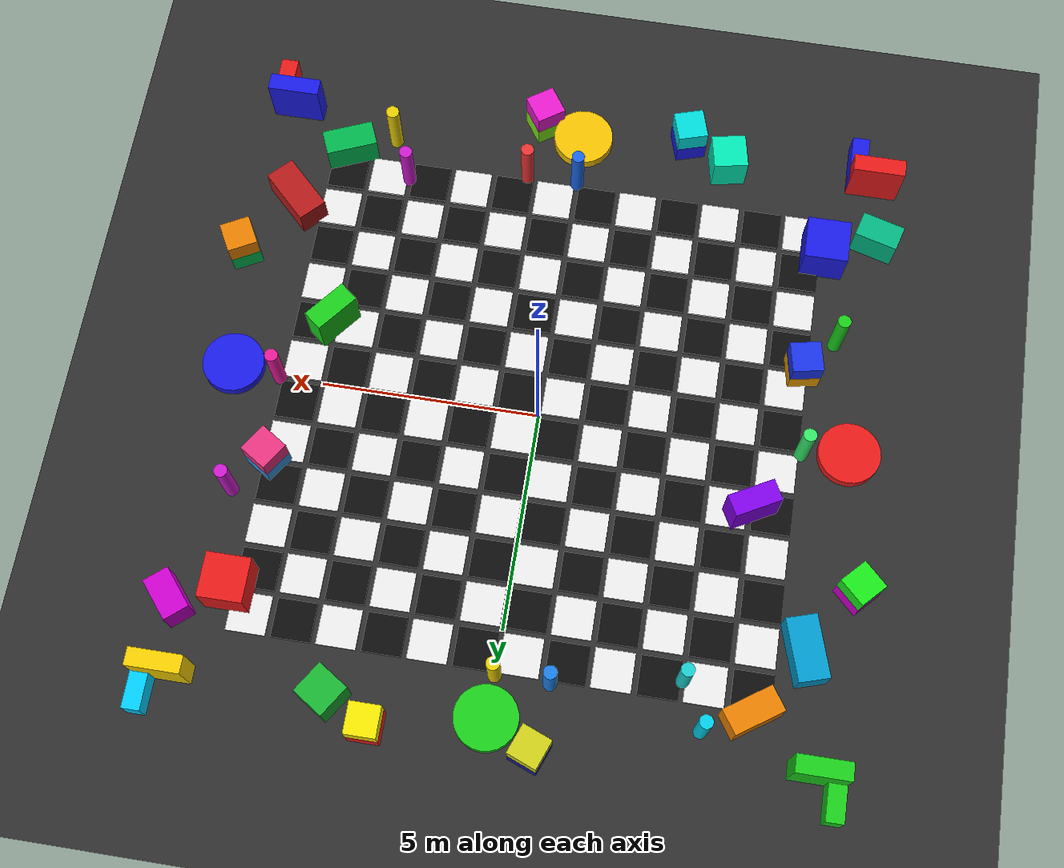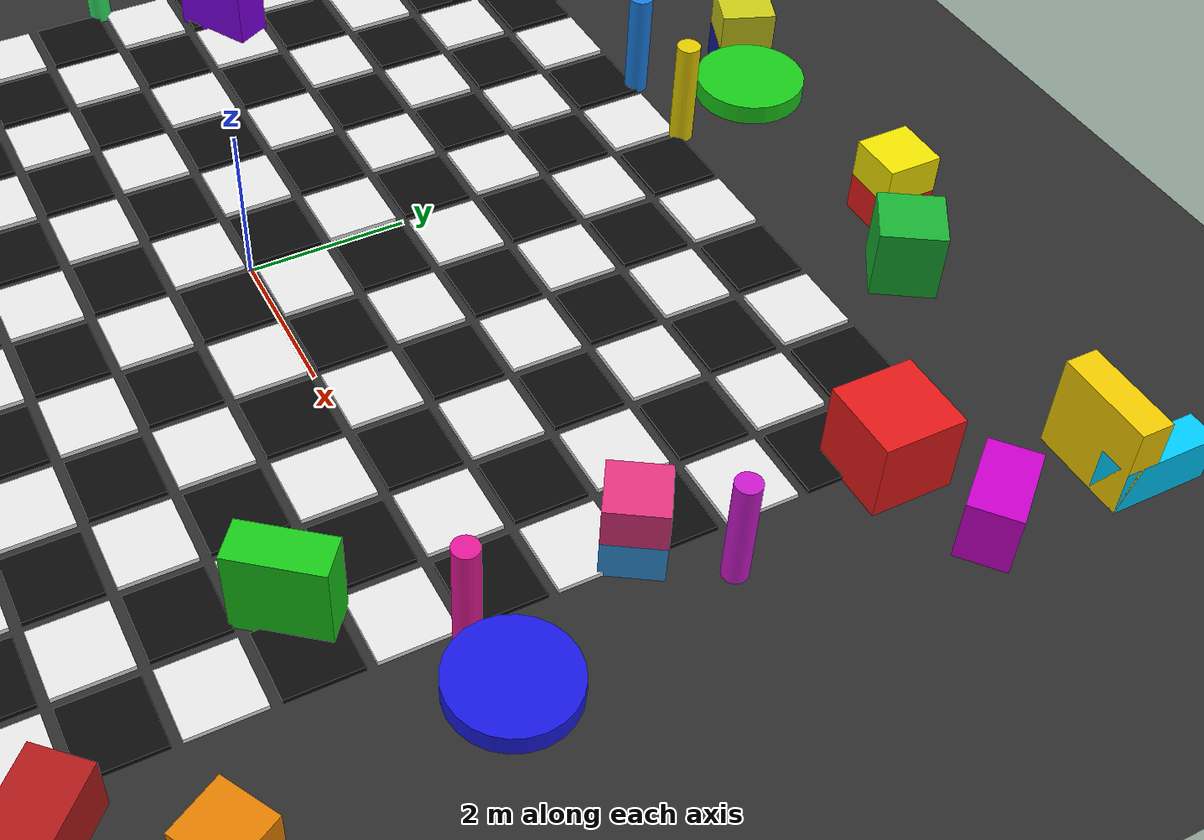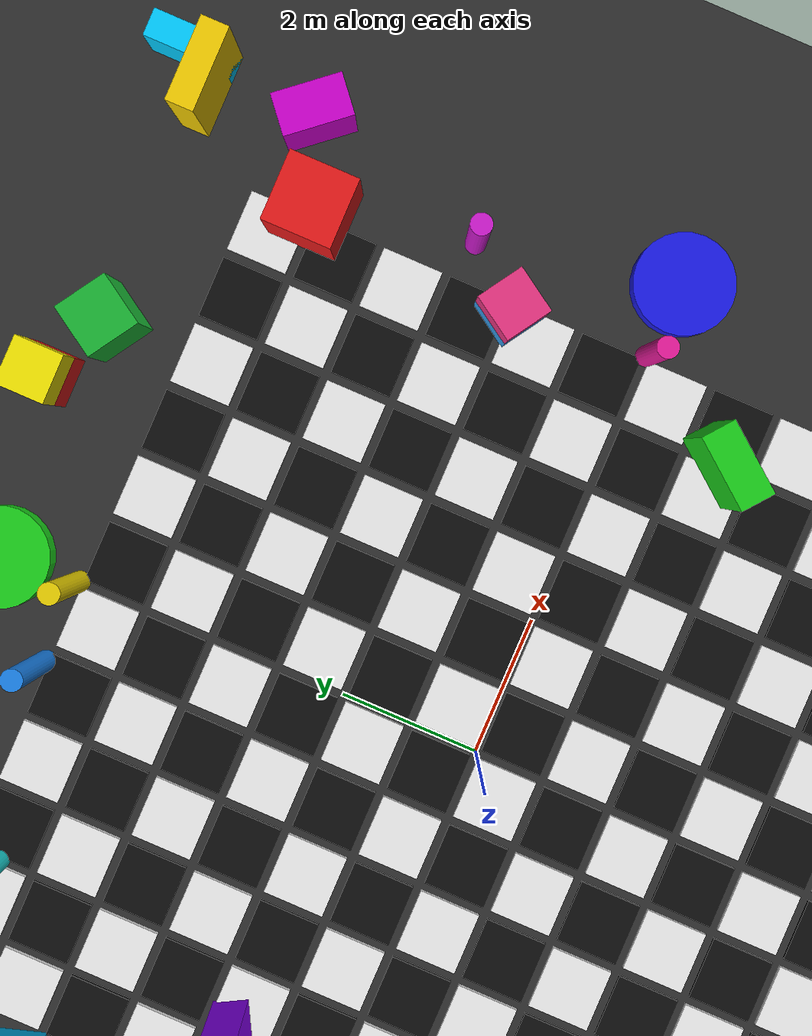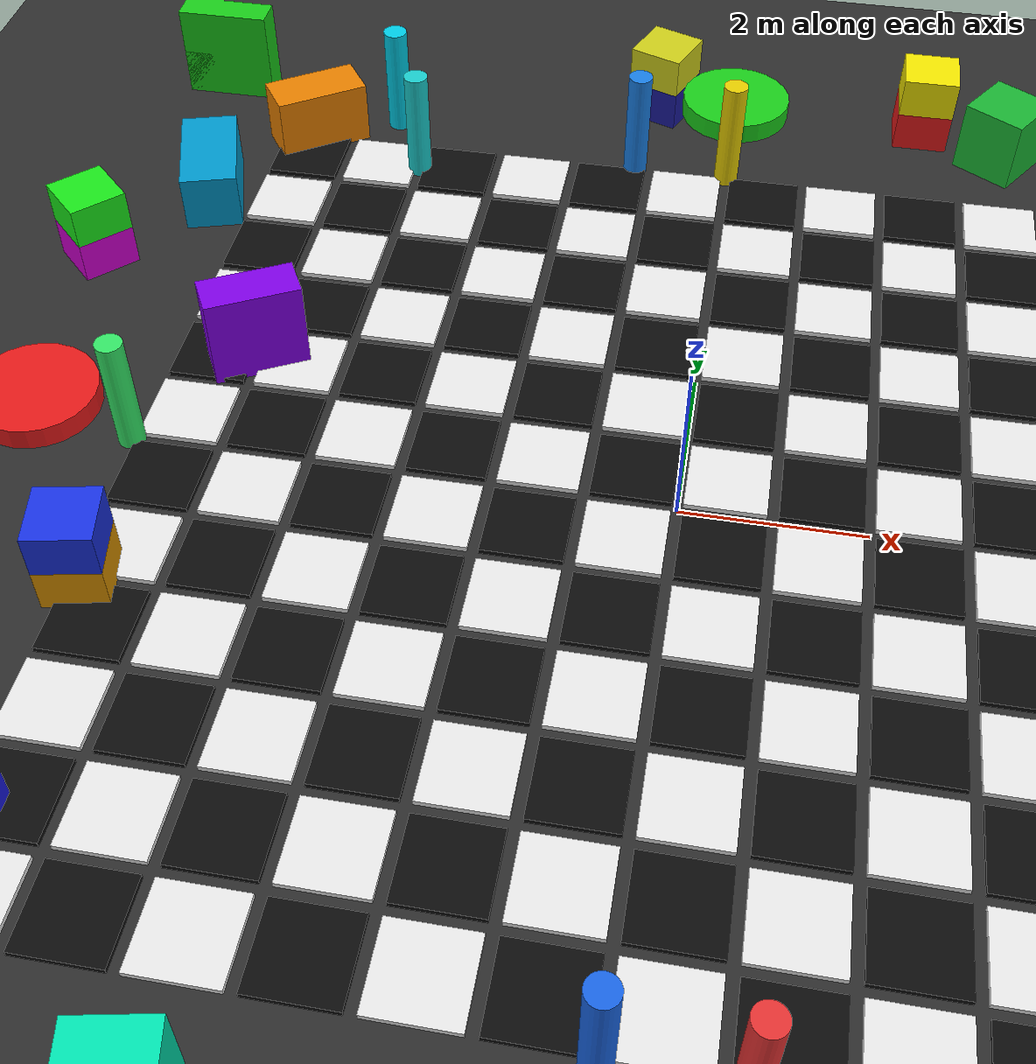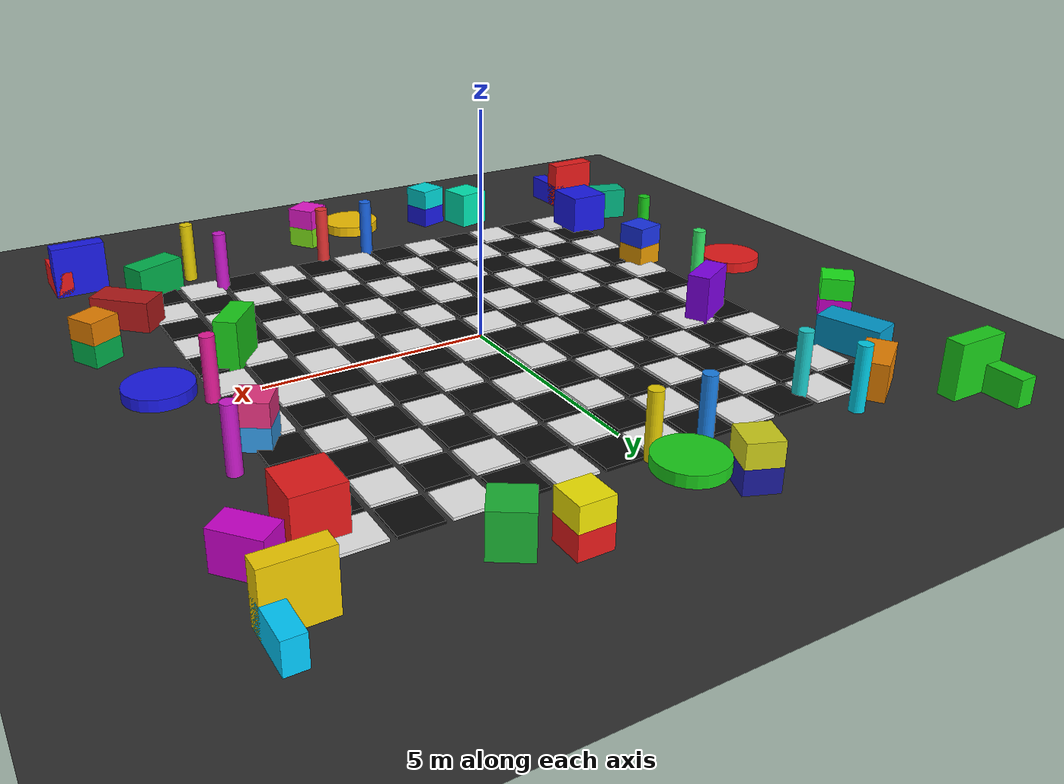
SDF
<?xml version="1.0" ?>
<sdf version="1.9">
  <world name="slam_world_realistic">

    <plugin filename="gz-sim-physics-system"
            name="gz::sim::systems::Physics"/>
    <plugin filename="gz-sim-user-commands-system"
            name="gz::sim::systems::UserCommands"/>
    <plugin filename="gz-sim-scene-broadcaster-system"
            name="gz::sim::systems::SceneBroadcaster"/>
    <plugin filename="gz-sim-sensors-system"
            name="gz::sim::systems::Sensors">
      <render_engine>ogre2</render_engine>
    </plugin>

    <gravity>0 0 -9.8</gravity>

    <scene>
      <ambient>0.40 0.40 0.40 1</ambient>
      <background>0.45 0.60 0.80 1</background>
      <shadows>true</shadows>
    </scene>

    <!-- Ana güneş: açılı, gölge aktif -->
    <light name="sun" type="directional">
      <pose>0 0 30 0 0 0</pose>
      <diffuse>1.0 0.98 0.92 1</diffuse>
      <specular>0.5 0.5 0.45 1</specular>
      <direction>-0.5 0.3 -1.0</direction>
      <cast_shadows>true</cast_shadows>
    </light>

    <!-- Dolgu ışığı: zayıf, gölgesiz -->
    <light name="fill_light" type="directional">
      <pose>0 0 20 0 0 0</pose>
      <diffuse>0.30 0.32 0.35 1</diffuse>
      <specular>0.05 0.05 0.05 1</specular>
      <direction>0.4 -0.3 -1.0</direction>
      <cast_shadows>false</cast_shadows>
    </light>

    <!-- Zemin düzlemi: koyu gri baz (checkerboard tile'ların altı) -->
    <model name="ground_plane">
      <static>true</static>
      <pose>0 0 0 0 0 0</pose>
      <link name="ground_link">
        <collision name="collision">
          <geometry>
            <plane><normal>0 0 1</normal><size>80 80</size></plane>
          </geometry>
        </collision>
        <visual name="visual">
          <geometry>
            <plane><normal>0 0 1</normal><size>80 80</size></plane>
          </geometry>
          <material>
            <ambient>0.15 0.15 0.15 1</ambient>
            <diffuse>0.18 0.18 0.18 1</diffuse>
            <specular>0.02 0.02 0.02 1</specular>
          </material>
        </visual>
      </link>
    </model>

    <model name="cb_0">
      <static>true</static>
      <pose>-5.500 -5.500 0.03 0 0 0</pose>
      <link name="link">
        <collision name="col"><geometry><box><size>0.88 0.88 0.06</size></box></geometry></collision>
        <visual name="vis">
          <geometry><box><size>0.88 0.88 0.06</size></box></geometry>
          <material>
            <ambient>0.910 0.910 0.910 1</ambient>
            <diffuse>0.910 0.910 0.910 1</diffuse>
            <specular>0.080 0.080 0.080 1</specular>
          </material>
        </visual>
      </link>
    </model>

    <model name="cb_1">
      <static>true</static>
      <pose>-5.500 -4.500 0.03 0 0 0</pose>
      <link name="link">
        <collision name="col"><geometry><box><size>0.88 0.88 0.06</size></box></geometry></collision>
        <visual name="vis">
          <geometry><box><size>0.88 0.88 0.06</size></box></geometry>
          <material>
            <ambient>0.050 0.050 0.050 1</ambient>
            <diffuse>0.050 0.050 0.050 1</diffuse>
            <specular>0.020 0.020 0.020 1</specular>
          </material>
        </visual>
      </link>
    </model>

    <model name="cb_2">
      <static>true</static>
      <pose>-5.500 -3.500 0.03 0 0 0</pose>
      <link name="link">
        <collision name="col"><geometry><box><size>0.88 0.88 0.06</size></box></geometry></collision>
        <visual name="vis">
          <geometry><box><size>0.88 0.88 0.06</size></box></geometry>
          <material>
            <ambient>0.910 0.910 0.910 1</ambient>
            <diffuse>0.910 0.910 0.910 1</diffuse>
            <specular>0.080 0.080 0.080 1</specular>
          </material>
        </visual>
      </link>
    </model>

    <model name="cb_3">
      <static>true</static>
      <pose>-5.500 -2.500 0.03 0 0 0</pose>
      <link name="link">
        <collision name="col"><geometry><box><size>0.88 0.88 0.06</size></box></geometry></collision>
        <visual name="vis">
          <geometry><box><size>0.88 0.88 0.06</size></box></geometry>
          <material>
            <ambient>0.050 0.050 0.050 1</ambient>
            <diffuse>0.050 0.050 0.050 1</diffuse>
            <specular>0.020 0.020 0.020 1</specular>
          </material>
        </visual>
      </link>
    </model>

    <model name="cb_4">
      <static>true</static>
      <pose>-5.500 -1.500 0.03 0 0 0</pose>
      <link name="link">
        <collision name="col"><geometry><box><size>0.88 0.88 0.06</size></box></geometry></collision>
        <visual name="vis">
          <geometry><box><size>0.88 0.88 0.06</size></box></geometry>
          <material>
            <ambient>0.910 0.910 0.910 1</ambient>
            <diffuse>0.910 0.910 0.910 1</diffuse>
            <specular>0.080 0.080 0.080 1</specular>
          </material>
        </visual>
      </link>
    </model>

    <model name="cb_5">
      <static>true</static>
      <pose>-5.500 -0.500 0.03 0 0 0</pose>
      <link name="link">
        <collision name="col"><geometry><box><size>0.88 0.88 0.06</size></box></geometry></collision>
        <visual name="vis">
          <geometry><box><size>0.88 0.88 0.06</size></box></geometry>
          <material>
            <ambient>0.050 0.050 0.050 1</ambient>
            <diffuse>0.050 0.050 0.050 1</diffuse>
            <specular>0.020 0.020 0.020 1</specular>
          </material>
        </visual>
      </link>
    </model>

    <model name="cb_6">
      <static>true</static>
      <pose>-5.500 0.500 0.03 0 0 0</pose>
      <link name="link">
        <collision name="col"><geometry><box><size>0.88 0.88 0.06</size></box></geometry></collision>
        <visual name="vis">
          <geometry><box><size>0.88 0.88 0.06</size></box></geometry>
          <material>
            <ambient>0.910 0.910 0.910 1</ambient>
            <diffuse>0.910 0.910 0.910 1</diffuse>
            <specular>0.080 0.080 0.080 1</specular>
          </material>
        </visual>
      </link>
    </model>

    <model name="cb_7">
      <static>true</static>
      <pose>-5.500 1.500 0.03 0 0 0</pose>
      <link name="link">
        <collision name="col"><geometry><box><size>0.88 0.88 0.06</size></box></geometry></collision>
        <visual name="vis">
          <geometry><box><size>0.88 0.88 0.06</size></box></geometry>
          <material>
            <ambient>0.050 0.050 0.050 1</ambient>
            <diffuse>0.050 0.050 0.050 1</diffuse>
            <specular>0.020 0.020 0.020 1</specular>
          </material>
        </visual>
      </link>
    </model>

    <model name="cb_8">
      <static>true</static>
      <pose>-5.500 2.500 0.03 0 0 0</pose>
      <link name="link">
        <collision name="col"><geometry><box><size>0.88 0.88 0.06</size></box></geometry></collision>
        <visual name="vis">
          <geometry><box><size>0.88 0.88 0.06</size></box></geometry>
          <material>
            <ambient>0.910 0.910 0.910 1</ambient>
            <diffuse>0.910 0.910 0.910 1</diffuse>
            <specular>0.080 0.080 0.080 1</specular>
          </material>
        </visual>
      </link>
    </model>

    <model name="cb_9">
      <static>true</static>
      <pose>-5.500 3.500 0.03 0 0 0</pose>
      <link name="link">
        <collision name="col"><geometry><box><size>0.88 0.88 0.06</size></box></geometry></collision>
        <visual name="vis">
          <geometry><box><size>0.88 0.88 0.06</size></box></geometry>
          <material>
            <ambient>0.050 0.050 0.050 1</ambient>
            <diffuse>0.050 0.050 0.050 1</diffuse>
            <specular>0.020 0.020 0.020 1</specular>
          </material>
        </visual>
      </link>
    </model>

    <model name="cb_10">
      <static>true</static>
      <pose>-5.500 4.500 0.03 0 0 0</pose>
      <link name="link">
        <collision name="col"><geometry><box><size>0.88 0.88 0.06</size></box></geometry></collision>
        <visual name="vis">
          <geometry><box><size>0.88 0.88 0.06</size></box></geometry>
          <material>
            <ambient>0.910 0.910 0.910 1</ambient>
            <diffuse>0.910 0.910 0.910 1</diffuse>
            <specular>0.080 0.080 0.080 1</specular>
          </material>
        </visual>
      </link>
    </model>

    <model name="cb_11">
      <static>true</static>
      <pose>-5.500 5.500 0.03 0 0 0</pose>
      <link name="link">
        <collision name="col"><geometry><box><size>0.88 0.88 0.06</size></box></geometry></collision>
        <visual name="vis">
          <geometry><box><size>0.88 0.88 0.06</size></box></geometry>
          <material>
            <ambient>0.050 0.050 0.050 1</ambient>
            <diffuse>0.050 0.050 0.050 1</diffuse>
            <specular>0.020 0.020 0.020 1</specular>
          </material>
        </visual>
      </link>
    </model>

    <model name="cb_12">
      <static>true</static>
      <pose>-4.500 -5.500 0.03 0 0 0</pose>
      <link name="link">
        <collision name="col"><geometry><box><size>0.88 0.88 0.06</size></box></geometry></collision>
        <visual name="vis">
          <geometry><box><size>0.88 0.88 0.06</size></box></geometry>
          <material>
            <ambient>0.050 0.050 0.050 1</ambient>
            <diffuse>0.050 0.050 0.050 1</diffuse>
            <specular>0.020 0.020 0.020 1</specular>
          </material>
        </visual>
      </link>
    </model>

    <model name="cb_13">
      <static>true</static>
      <pose>-4.500 -4.500 0.03 0 0 0</pose>
      <link name="link">
        <collision name="col"><geometry><box><size>0.88 0.88 0.06</size></box></geometry></collision>
        <visual name="vis">
          <geometry><box><size>0.88 0.88 0.06</size></box></geometry>
          <material>
            <ambient>0.910 0.910 0.910 1</ambient>
            <diffuse>0.910 0.910 0.910 1</diffuse>
            <specular>0.080 0.080 0.080 1</specular>
          </material>
        </visual>
      </link>
    </model>

    <model name="cb_14">
      <static>true</static>
      <pose>-4.500 -3.500 0.03 0 0 0</pose>
      <link name="link">
        <collision name="col"><geometry><box><size>0.88 0.88 0.06</size></box></geometry></collision>
        <visual name="vis">
          <geometry><box><size>0.88 0.88 0.06</size></box></geometry>
          <material>
            <ambient>0.050 0.050 0.050 1</ambient>
            <diffuse>0.050 0.050 0.050 1</diffuse>
            <specular>0.020 0.020 0.020 1</specular>
          </material>
        </visual>
      </link>
    </model>

    <model name="cb_15">
      <static>true</static>
      <pose>-4.500 -2.500 0.03 0 0 0</pose>
      <link name="link">
        <collision name="col"><geometry><box><size>0.88 0.88 0.06</size></box></geometry></collision>
        <visual name="vis">
          <geometry><box><size>0.88 0.88 0.06</size></box></geometry>
          <material>
            <ambient>0.910 0.910 0.910 1</ambient>
            <diffuse>0.910 0.910 0.910 1</diffuse>
            <specular>0.080 0.080 0.080 1</specular>
          </material>
        </visual>
      </link>
    </model>

    <model name="cb_16">
      <static>true</static>
      <pose>-4.500 -1.500 0.03 0 0 0</pose>
      <link name="link">
        <collision name="col"><geometry><box><size>0.88 0.88 0.06</size></box></geometry></collision>
        <visual name="vis">
          <geometry><box><size>0.88 0.88 0.06</size></box></geometry>
          <material>
            <ambient>0.050 0.050 0.050 1</ambient>
            <diffuse>0.050 0.050 0.050 1</diffuse>
            <specular>0.020 0.020 0.020 1</specular>
          </material>
        </visual>
      </link>
    </model>

    <model name="cb_17">
      <static>true</static>
      <pose>-4.500 -0.500 0.03 0 0 0</pose>
      <link name="link">
        <collision name="col"><geometry><box><size>0.88 0.88 0.06</size></box></geometry></collision>
        <visual name="vis">
          <geometry><box><size>0.88 0.88 0.06</size></box></geometry>
          <material>
            <ambient>0.910 0.910 0.910 1</ambient>
            <diffuse>0.910 0.910 0.910 1</diffuse>
            <specular>0.080 0.080 0.080 1</specular>
          </material>
        </visual>
      </link>
    </model>

    <model name="cb_18">
      <static>true</static>
      <pose>-4.500 0.500 0.03 0 0 0</pose>
      <link name="link">
        <collision name="col"><geometry><box><size>0.88 0.88 0.06</size></box></geometry></collision>
        <visual name="vis">
          <geometry><box><size>0.88 0.88 0.06</size></box></geometry>
          <material>
            <ambient>0.050 0.050 0.050 1</ambient>
            <diffuse>0.050 0.050 0.050 1</diffuse>
            <specular>0.020 0.020 0.020 1</specular>
          </material>
        </visual>
      </link>
    </model>

    <model name="cb_19">
      <static>true</static>
      <pose>-4.500 1.500 0.03 0 0 0</pose>
      <link name="link">
        <collision name="col"><geometry><box><size>0.88 0.88 0.06</size></box></geometry></collision>
        <visual name="vis">
          <geometry><box><size>0.88 0.88 0.06</size></box></geometry>
          <material>
            <ambient>0.910 0.910 0.910 1</ambient>
            <diffuse>0.910 0.910 0.910 1</diffuse>
            <specular>0.080 0.080 0.080 1</specular>
          </material>
        </visual>
      </link>
    </model>

    <model name="cb_20">
      <static>true</static>
      <pose>-4.500 2.500 0.03 0 0 0</pose>
      <link name="link">
        <collision name="col"><geometry><box><size>0.88 0.88 0.06</size></box></geometry></collision>
        <visual name="vis">
          <geometry><box><size>0.88 0.88 0.06</size></box></geometry>
          <material>
            <ambient>0.050 0.050 0.050 1</ambient>
            <diffuse>0.050 0.050 0.050 1</diffuse>
            <specular>0.020 0.020 0.020 1</specular>
          </material>
        </visual>
      </link>
    </model>

    <model name="cb_21">
      <static>true</static>
      <pose>-4.500 3.500 0.03 0 0 0</pose>
      <link name="link">
        <collision name="col"><geometry><box><size>0.88 0.88 0.06</size></box></geometry></collision>
        <visual name="vis">
          <geometry><box><size>0.88 0.88 0.06</size></box></geometry>
          <material>
            <ambient>0.910 0.910 0.910 1</ambient>
            <diffuse>0.910 0.910 0.910 1</diffuse>
            <specular>0.080 0.080 0.080 1</specular>
          </material>
        </visual>
      </link>
    </model>

    <model name="cb_22">
      <static>true</static>
      <pose>-4.500 4.500 0.03 0 0 0</pose>
      <link name="link">
        <collision name="col"><geometry><box><size>0.88 0.88 0.06</size></box></geometry></collision>
        <visual name="vis">
          <geometry><box><size>0.88 0.88 0.06</size></box></geometry>
          <material>
            <ambient>0.050 0.050 0.050 1</ambient>
            <diffuse>0.050 0.050 0.050 1</diffuse>
            <specular>0.020 0.020 0.020 1</specular>
          </material>
        </visual>
      </link>
    </model>

    <model name="cb_23">
      <static>true</static>
      <pose>-4.500 5.500 0.03 0 0 0</pose>
      <link name="link">
        <collision name="col"><geometry><box><size>0.88 0.88 0.06</size></box></geometry></collision>
        <visual name="vis">
          <geometry><box><size>0.88 0.88 0.06</size></box></geometry>
          <material>
            <ambient>0.910 0.910 0.910 1</ambient>
            <diffuse>0.910 0.910 0.910 1</diffuse>
            <specular>0.080 0.080 0.080 1</specular>
          </material>
        </visual>
      </link>
    </model>

    <model name="cb_24">
      <static>true</static>
      <pose>-3.500 -5.500 0.03 0 0 0</pose>
      <link name="link">
        <collision name="col"><geometry><box><size>0.88 0.88 0.06</size></box></geometry></collision>
        <visual name="vis">
          <geometry><box><size>0.88 0.88 0.06</size></box></geometry>
          <material>
            <ambient>0.910 0.910 0.910 1</ambient>
            <diffuse>0.910 0.910 0.910 1</diffuse>
            <specular>0.080 0.080 0.080 1</specular>
          </material>
        </visual>
      </link>
    </model>

    <model name="cb_25">
      <static>true</static>
      <pose>-3.500 -4.500 0.03 0 0 0</pose>
      <link name="link">
        <collision name="col"><geometry><box><size>0.88 0.88 0.06</size></box></geometry></collision>
        <visual name="vis">
          <geometry><box><size>0.88 0.88 0.06</size></box></geometry>
          <material>
            <ambient>0.050 0.050 0.050 1</ambient>
            <diffuse>0.050 0.050 0.050 1</diffuse>
            <specular>0.020 0.020 0.020 1</specular>
          </material>
        </visual>
      </link>
    </model>

    <model name="cb_26">
      <static>true</static>
      <pose>-3.500 -3.500 0.03 0 0 0</pose>
      <link name="link">
        <collision name="col"><geometry><box><size>0.88 0.88 0.06</size></box></geometry></collision>
        <visual name="vis">
          <geometry><box><size>0.88 0.88 0.06</size></box></geometry>
          <material>
            <ambient>0.910 0.910 0.910 1</ambient>
            <diffuse>0.910 0.910 0.910 1</diffuse>
            <specular>0.080 0.080 0.080 1</specular>
          </material>
        </visual>
      </link>
    </model>

    <model name="cb_27">
      <static>true</static>
      <pose>-3.500 -2.500 0.03 0 0 0</pose>
      <link name="link">
        <collision name="col"><geometry><box><size>0.88 0.88 0.06</size></box></geometry></collision>
        <visual name="vis">
          <geometry><box><size>0.88 0.88 0.06</size></box></geometry>
          <material>
            <ambient>0.050 0.050 0.050 1</ambient>
            <diffuse>0.050 0.050 0.050 1</diffuse>
            <specular>0.020 0.020 0.020 1</specular>
          </material>
        </visual>
      </link>
    </model>

    <model name="cb_28">
      <static>true</static>
      <pose>-3.500 -1.500 0.03 0 0 0</pose>
      <link name="link">
        <collision name="col"><geometry><box><size>0.88 0.88 0.06</size></box></geometry></collision>
        <visual name="vis">
          <geometry><box><size>0.88 0.88 0.06</size></box></geometry>
          <material>
            <ambient>0.910 0.910 0.910 1</ambient>
            <diffuse>0.910 0.910 0.910 1</diffuse>
            <specular>0.080 0.080 0.080 1</specular>
          </material>
        </visual>
      </link>
    </model>

    <model name="cb_29">
      <static>true</static>
      <pose>-3.500 -0.500 0.03 0 0 0</pose>
      <link name="link">
        <collision name="col"><geometry><box><size>0.88 0.88 0.06</size></box></geometry></collision>
        <visual name="vis">
          <geometry><box><size>0.88 0.88 0.06</size></box></geometry>
          <material>
            <ambient>0.050 0.050 0.050 1</ambient>
            <diffuse>0.050 0.050 0.050 1</diffuse>
            <specular>0.020 0.020 0.020 1</specular>
          </material>
        </visual>
      </link>
    </model>

    <model name="cb_30">
      <static>true</static>
      <pose>-3.500 0.500 0.03 0 0 0</pose>
      <link name="link">
        <collision name="col"><geometry><box><size>0.88 0.88 0.06</size></box></geometry></collision>
        <visual name="vis">
          <geometry><box><size>0.88 0.88 0.06</size></box></geometry>
          <material>
            <ambient>0.910 0.910 0.910 1</ambient>
            <diffuse>0.910 0.910 0.910 1</diffuse>
            <specular>0.080 0.080 0.080 1</specular>
          </material>
        </visual>
      </link>
    </model>

    <model name="cb_31">
      <static>true</static>
      <pose>-3.500 1.500 0.03 0 0 0</pose>
      <link name="link">
        <collision name="col"><geometry><box><size>0.88 0.88 0.06</size></box></geometry></collision>
        <visual name="vis">
          <geometry><box><size>0.88 0.88 0.06</size></box></geometry>
          <material>
            <ambient>0.050 0.050 0.050 1</ambient>
            <diffuse>0.050 0.050 0.050 1</diffuse>
            <specular>0.020 0.020 0.020 1</specular>
          </material>
        </visual>
      </link>
    </model>

    <model name="cb_32">
      <static>true</static>
      <pose>-3.500 2.500 0.03 0 0 0</pose>
      <link name="link">
        <collision name="col"><geometry><box><size>0.88 0.88 0.06</size></box></geometry></collision>
        <visual name="vis">
          <geometry><box><size>0.88 0.88 0.06</size></box></geometry>
          <material>
            <ambient>0.910 0.910 0.910 1</ambient>
            <diffuse>0.910 0.910 0.910 1</diffuse>
            <specular>0.080 0.080 0.080 1</specular>
          </material>
        </visual>
      </link>
    </model>

    <model name="cb_33">
      <static>true</static>
      <pose>-3.500 3.500 0.03 0 0 0</pose>
      <link name="link">
        <collision name="col"><geometry><box><size>0.88 0.88 0.06</size></box></geometry></collision>
        <visual name="vis">
          <geometry><box><size>0.88 0.88 0.06</size></box></geometry>
          <material>
            <ambient>0.050 0.050 0.050 1</ambient>
            <diffuse>0.050 0.050 0.050 1</diffuse>
            <specular>0.020 0.020 0.020 1</specular>
          </material>
        </visual>
      </link>
    </model>

    <model name="cb_34">
      <static>true</static>
      <pose>-3.500 4.500 0.03 0 0 0</pose>
      <link name="link">
        <collision name="col"><geometry><box><size>0.88 0.88 0.06</size></box></geometry></collision>
        <visual name="vis">
          <geometry><box><size>0.88 0.88 0.06</size></box></geometry>
          <material>
            <ambient>0.910 0.910 0.910 1</ambient>
            <diffuse>0.910 0.910 0.910 1</diffuse>
            <specular>0.080 0.080 0.080 1</specular>
          </material>
        </visual>
      </link>
    </model>

    <model name="cb_35">
      <static>true</static>
      <pose>-3.500 5.500 0.03 0 0 0</pose>
      <link name="link">
        <collision name="col"><geometry><box><size>0.88 0.88 0.06</size></box></geometry></collision>
        <visual name="vis">
          <geometry><box><size>0.88 0.88 0.06</size></box></geometry>
          <material>
            <ambient>0.050 0.050 0.050 1</ambient>
            <diffuse>0.050 0.050 0.050 1</diffuse>
            <specular>0.020 0.020 0.020 1</specular>
          </material>
        </visual>
      </link>
    </model>

    <model name="cb_36">
      <static>true</static>
      <pose>-2.500 -5.500 0.03 0 0 0</pose>
      <link name="link">
        <collision name="col"><geometry><box><size>0.88 0.88 0.06</size></box></geometry></collision>
        <visual name="vis">
          <geometry><box><size>0.88 0.88 0.06</size></box></geometry>
          <material>
            <ambient>0.050 0.050 0.050 1</ambient>
            <diffuse>0.050 0.050 0.050 1</diffuse>
            <specular>0.020 0.020 0.020 1</specular>
          </material>
        </visual>
      </link>
    </model>

    <model name="cb_37">
      <static>true</static>
      <pose>-2.500 -4.500 0.03 0 0 0</pose>
      <link name="link">
        <collision name="col"><geometry><box><size>0.88 0.88 0.06</size></box></geometry></collision>
        <visual name="vis">
          <geometry><box><size>0.88 0.88 0.06</size></box></geometry>
          <material>
            <ambient>0.910 0.910 0.910 1</ambient>
            <diffuse>0.910 0.910 0.910 1</diffuse>
            <specular>0.080 0.080 0.080 1</specular>
          </material>
        </visual>
      </link>
    </model>

    <model name="cb_38">
      <static>true</static>
      <pose>-2.500 -3.500 0.03 0 0 0</pose>
      <link name="link">
        <collision name="col"><geometry><box><size>0.88 0.88 0.06</size></box></geometry></collision>
        <visual name="vis">
          <geometry><box><size>0.88 0.88 0.06</size></box></geometry>
          <material>
            <ambient>0.050 0.050 0.050 1</ambient>
            <diffuse>0.050 0.050 0.050 1</diffuse>
            <specular>0.020 0.020 0.020 1</specular>
          </material>
        </visual>
      </link>
    </model>

    <model name="cb_39">
      <static>true</static>
      <pose>-2.500 -2.500 0.03 0 0 0</pose>
      <link name="link">
        <collision name="col"><geometry><box><size>0.88 0.88 0.06</size></box></geometry></collision>
        <visual name="vis">
          <geometry><box><size>0.88 0.88 0.06</size></box></geometry>
          <material>
            <ambient>0.910 0.910 0.910 1</ambient>
            <diffuse>0.910 0.910 0.910 1</diffuse>
            <specular>0.080 0.080 0.080 1</specular>
          </material>
        </visual>
      </link>
    </model>

    <model name="cb_40">
      <static>true</static>
      <pose>-2.500 -1.500 0.03 0 0 0</pose>
      <link name="link">
        <collision name="col"><geometry><box><size>0.88 0.88 0.06</size></box></geometry></collision>
        <visual name="vis">
          <geometry><box><size>0.88 0.88 0.06</size></box></geometry>
          <material>
            <ambient>0.050 0.050 0.050 1</ambient>
            <diffuse>0.050 0.050 0.050 1</diffuse>
            <specular>0.020 0.020 0.020 1</specular>
          </material>
        </visual>
      </link>
    </model>

    <model name="cb_41">
      <static>true</static>
      <pose>-2.500 -0.500 0.03 0 0 0</pose>
      <link name="link">
        <collision name="col"><geometry><box><size>0.88 0.88 0.06</size></box></geometry></collision>
        <visual name="vis">
          <geometry><box><size>0.88 0.88 0.06</size></box></geometry>
          <material>
            <ambient>0.910 0.910 0.910 1</ambient>
            <diffuse>0.910 0.910 0.910 1</diffuse>
            <specular>0.080 0.080 0.080 1</specular>
          </material>
        </visual>
      </link>
    </model>

    <model name="cb_42">
      <static>true</static>
      <pose>-2.500 0.500 0.03 0 0 0</pose>
      <link name="link">
        <collision name="col"><geometry><box><size>0.88 0.88 0.06</size></box></geometry></collision>
        <visual name="vis">
          <geometry><box><size>0.88 0.88 0.06</size></box></geometry>
          <material>
            <ambient>0.050 0.050 0.050 1</ambient>
            <diffuse>0.050 0.050 0.050 1</diffuse>
            <specular>0.020 0.020 0.020 1</specular>
          </material>
        </visual>
      </link>
    </model>

    <model name="cb_43">
      <static>true</static>
      <pose>-2.500 1.500 0.03 0 0 0</pose>
      <link name="link">
        <collision name="col"><geometry><box><size>0.88 0.88 0.06</size></box></geometry></collision>
        <visual name="vis">
          <geometry><box><size>0.88 0.88 0.06</size></box></geometry>
          <material>
            <ambient>0.910 0.910 0.910 1</ambient>
            <diffuse>0.910 0.910 0.910 1</diffuse>
            <specular>0.080 0.080 0.080 1</specular>
          </material>
        </visual>
      </link>
    </model>

    <model name="cb_44">
      <static>true</static>
      <pose>-2.500 2.500 0.03 0 0 0</pose>
      <link name="link">
        <collision name="col"><geometry><box><size>0.88 0.88 0.06</size></box></geometry></collision>
        <visual name="vis">
          <geometry><box><size>0.88 0.88 0.06</size></box></geometry>
          <material>
            <ambient>0.050 0.050 0.050 1</ambient>
            <diffuse>0.050 0.050 0.050 1</diffuse>
            <specular>0.020 0.020 0.020 1</specular>
          </material>
        </visual>
      </link>
    </model>

    <model name="cb_45">
      <static>true</static>
      <pose>-2.500 3.500 0.03 0 0 0</pose>
      <link name="link">
        <collision name="col"><geometry><box><size>0.88 0.88 0.06</size></box></geometry></collision>
        <visual name="vis">
          <geometry><box><size>0.88 0.88 0.06</size></box></geometry>
          <material>
            <ambient>0.910 0.910 0.910 1</ambient>
            <diffuse>0.910 0.910 0.910 1</diffuse>
            <specular>0.080 0.080 0.080 1</specular>
          </material>
        </visual>
      </link>
    </model>

    <model name="cb_46">
      <static>true</static>
      <pose>-2.500 4.500 0.03 0 0 0</pose>
      <link name="link">
        <collision name="col"><geometry><box><size>0.88 0.88 0.06</size></box></geometry></collision>
        <visual name="vis">
          <geometry><box><size>0.88 0.88 0.06</size></box></geometry>
          <material>
            <ambient>0.050 0.050 0.050 1</ambient>
            <diffuse>0.050 0.050 0.050 1</diffuse>
            <specular>0.020 0.020 0.020 1</specular>
          </material>
        </visual>
      </link>
    </model>

    <model name="cb_47">
      <static>true</static>
      <pose>-2.500 5.500 0.03 0 0 0</pose>
      <link name="link">
        <collision name="col"><geometry><box><size>0.88 0.88 0.06</size></box></geometry></collision>
        <visual name="vis">
          <geometry><box><size>0.88 0.88 0.06</size></box></geometry>
          <material>
            <ambient>0.910 0.910 0.910 1</ambient>
            <diffuse>0.910 0.910 0.910 1</diffuse>
            <specular>0.080 0.080 0.080 1</specular>
          </material>
        </visual>
      </link>
    </model>

    <model name="cb_48">
      <static>true</static>
      <pose>-1.500 -5.500 0.03 0 0 0</pose>
      <link name="link">
        <collision name="col"><geometry><box><size>0.88 0.88 0.06</size></box></geometry></collision>
        <visual name="vis">
          <geometry><box><size>0.88 0.88 0.06</size></box></geometry>
          <material>
            <ambient>0.910 0.910 0.910 1</ambient>
            <diffuse>0.910 0.910 0.910 1</diffuse>
            <specular>0.080 0.080 0.080 1</specular>
          </material>
        </visual>
      </link>
    </model>

    <model name="cb_49">
      <static>true</static>
      <pose>-1.500 -4.500 0.03 0 0 0</pose>
      <link name="link">
        <collision name="col"><geometry><box><size>0.88 0.88 0.06</size></box></geometry></collision>
        <visual name="vis">
          <geometry><box><size>0.88 0.88 0.06</size></box></geometry>
          <material>
            <ambient>0.050 0.050 0.050 1</ambient>
            <diffuse>0.050 0.050 0.050 1</diffuse>
            <specular>0.020 0.020 0.020 1</specular>
          </material>
        </visual>
      </link>
    </model>

    <model name="cb_50">
      <static>true</static>
      <pose>-1.500 -3.500 0.03 0 0 0</pose>
      <link name="link">
        <collision name="col"><geometry><box><size>0.88 0.88 0.06</size></box></geometry></collision>
        <visual name="vis">
          <geometry><box><size>0.88 0.88 0.06</size></box></geometry>
          <material>
            <ambient>0.910 0.910 0.910 1</ambient>
            <diffuse>0.910 0.910 0.910 1</diffuse>
            <specular>0.080 0.080 0.080 1</specular>
          </material>
        </visual>
      </link>
    </model>

    <model name="cb_51">
      <static>true</static>
      <pose>-1.500 -2.500 0.03 0 0 0</pose>
      <link name="link">
        <collision name="col"><geometry><box><size>0.88 0.88 0.06</size></box></geometry></collision>
        <visual name="vis">
          <geometry><box><size>0.88 0.88 0.06</size></box></geometry>
          <material>
            <ambient>0.050 0.050 0.050 1</ambient>
            <diffuse>0.050 0.050 0.050 1</diffuse>
            <specular>0.020 0.020 0.020 1</specular>
          </material>
        </visual>
      </link>
    </model>

    <model name="cb_52">
      <static>true</static>
      <pose>-1.500 -1.500 0.03 0 0 0</pose>
      <link name="link">
        <collision name="col"><geometry><box><size>0.88 0.88 0.06</size></box></geometry></collision>
        <visual name="vis">
          <geometry><box><size>0.88 0.88 0.06</size></box></geometry>
          <material>
            <ambient>0.910 0.910 0.910 1</ambient>
            <diffuse>0.910 0.910 0.910 1</diffuse>
            <specular>0.080 0.080 0.080 1</specular>
          </material>
        </visual>
      </link>
    </model>

    <model name="cb_53">
      <static>true</static>
      <pose>-1.500 -0.500 0.03 0 0 0</pose>
      <link name="link">
        <collision name="col"><geometry><box><size>0.88 0.88 0.06</size></box></geometry></collision>
        <visual name="vis">
          <geometry><box><size>0.88 0.88 0.06</size></box></geometry>
          <material>
            <ambient>0.050 0.050 0.050 1</ambient>
            <diffuse>0.050 0.050 0.050 1</diffuse>
            <specular>0.020 0.020 0.020 1</specular>
          </material>
        </visual>
      </link>
    </model>

    <model name="cb_54">
      <static>true</static>
      <pose>-1.500 0.500 0.03 0 0 0</pose>
      <link name="link">
        <collision name="col"><geometry><box><size>0.88 0.88 0.06</size></box></geometry></collision>
        <visual name="vis">
          <geometry><box><size>0.88 0.88 0.06</size></box></geometry>
          <material>
            <ambient>0.910 0.910 0.910 1</ambient>
            <diffuse>0.910 0.910 0.910 1</diffuse>
            <specular>0.080 0.080 0.080 1</specular>
          </material>
        </visual>
      </link>
    </model>

    <model name="cb_55">
      <static>true</static>
      <pose>-1.500 1.500 0.03 0 0 0</pose>
      <link name="link">
        <collision name="col"><geometry><box><size>0.88 0.88 0.06</size></box></geometry></collision>
        <visual name="vis">
          <geometry><box><size>0.88 0.88 0.06</size></box></geometry>
          <material>
            <ambient>0.050 0.050 0.050 1</ambient>
            <diffuse>0.050 0.050 0.050 1</diffuse>
            <specular>0.020 0.020 0.020 1</specular>
          </material>
        </visual>
      </link>
    </model>

    <model name="cb_56">
      <static>true</static>
      <pose>-1.500 2.500 0.03 0 0 0</pose>
      <link name="link">
        <collision name="col"><geometry><box><size>0.88 0.88 0.06</size></box></geometry></collision>
        <visual name="vis">
          <geometry><box><size>0.88 0.88 0.06</size></box></geometry>
          <material>
            <ambient>0.910 0.910 0.910 1</ambient>
            <diffuse>0.910 0.910 0.910 1</diffuse>
            <specular>0.080 0.080 0.080 1</specular>
          </material>
        </visual>
      </link>
    </model>

    <model name="cb_57">
      <static>true</static>
      <pose>-1.500 3.500 0.03 0 0 0</pose>
      <link name="link">
        <collision name="col"><geometry><box><size>0.88 0.88 0.06</size></box></geometry></collision>
        <visual name="vis">
          <geometry><box><size>0.88 0.88 0.06</size></box></geometry>
          <material>
            <ambient>0.050 0.050 0.050 1</ambient>
            <diffuse>0.050 0.050 0.050 1</diffuse>
            <specular>0.020 0.020 0.020 1</specular>
          </material>
        </visual>
      </link>
    </model>

    <model name="cb_58">
      <static>true</static>
      <pose>-1.500 4.500 0.03 0 0 0</pose>
      <link name="link">
        <collision name="col"><geometry><box><size>0.88 0.88 0.06</size></box></geometry></collision>
        <visual name="vis">
          <geometry><box><size>0.88 0.88 0.06</size></box></geometry>
          <material>
            <ambient>0.910 0.910 0.910 1</ambient>
            <diffuse>0.910 0.910 0.910 1</diffuse>
            <specular>0.080 0.080 0.080 1</specular>
          </material>
        </visual>
      </link>
    </model>

    <model name="cb_59">
      <static>true</static>
      <pose>-1.500 5.500 0.03 0 0 0</pose>
      <link name="link">
        <collision name="col"><geometry><box><size>0.88 0.88 0.06</size></box></geometry></collision>
        <visual name="vis">
          <geometry><box><size>0.88 0.88 0.06</size></box></geometry>
          <material>
            <ambient>0.050 0.050 0.050 1</ambient>
            <diffuse>0.050 0.050 0.050 1</diffuse>
            <specular>0.020 0.020 0.020 1</specular>
          </material>
        </visual>
      </link>
    </model>

    <model name="cb_60">
      <static>true</static>
      <pose>-0.500 -5.500 0.03 0 0 0</pose>
      <link name="link">
        <collision name="col"><geometry><box><size>0.88 0.88 0.06</size></box></geometry></collision>
        <visual name="vis">
          <geometry><box><size>0.88 0.88 0.06</size></box></geometry>
          <material>
            <ambient>0.050 0.050 0.050 1</ambient>
            <diffuse>0.050 0.050 0.050 1</diffuse>
            <specular>0.020 0.020 0.020 1</specular>
          </material>
        </visual>
      </link>
    </model>

    <model name="cb_61">
      <static>true</static>
      <pose>-0.500 -4.500 0.03 0 0 0</pose>
      <link name="link">
        <collision name="col"><geometry><box><size>0.88 0.88 0.06</size></box></geometry></collision>
        <visual name="vis">
          <geometry><box><size>0.88 0.88 0.06</size></box></geometry>
          <material>
            <ambient>0.910 0.910 0.910 1</ambient>
            <diffuse>0.910 0.910 0.910 1</diffuse>
            <specular>0.080 0.080 0.080 1</specular>
          </material>
        </visual>
      </link>
    </model>

    <model name="cb_62">
      <static>true</static>
      <pose>-0.500 -3.500 0.03 0 0 0</pose>
      <link name="link">
        <collision name="col"><geometry><box><size>0.88 0.88 0.06</size></box></geometry></collision>
        <visual name="vis">
          <geometry><box><size>0.88 0.88 0.06</size></box></geometry>
          <material>
            <ambient>0.050 0.050 0.050 1</ambient>
            <diffuse>0.050 0.050 0.050 1</diffuse>
            <specular>0.020 0.020 0.020 1</specular>
          </material>
        </visual>
      </link>
    </model>

    <model name="cb_63">
      <static>true</static>
      <pose>-0.500 -2.500 0.03 0 0 0</pose>
      <link name="link">
        <collision name="col"><geometry><box><size>0.88 0.88 0.06</size></box></geometry></collision>
        <visual name="vis">
          <geometry><box><size>0.88 0.88 0.06</size></box></geometry>
          <material>
            <ambient>0.910 0.910 0.910 1</ambient>
            <diffuse>0.910 0.910 0.910 1</diffuse>
            <specular>0.080 0.080 0.080 1</specular>
          </material>
        </visual>
      </link>
    </model>

    <model name="cb_64">
      <static>true</static>
      <pose>-0.500 -1.500 0.03 0 0 0</pose>
      <link name="link">
        <collision name="col"><geometry><box><size>0.88 0.88 0.06</size></box></geometry></collision>
        <visual name="vis">
          <geometry><box><size>0.88 0.88 0.06</size></box></geometry>
          <material>
            <ambient>0.050 0.050 0.050 1</ambient>
            <diffuse>0.050 0.050 0.050 1</diffuse>
            <specular>0.020 0.020 0.020 1</specular>
          </material>
        </visual>
      </link>
    </model>

    <model name="cb_65">
      <static>true</static>
      <pose>-0.500 -0.500 0.03 0 0 0</pose>
      <link name="link">
        <collision name="col"><geometry><box><size>0.88 0.88 0.06</size></box></geometry></collision>
        <visual name="vis">
          <geometry><box><size>0.88 0.88 0.06</size></box></geometry>
          <material>
            <ambient>0.910 0.910 0.910 1</ambient>
            <diffuse>0.910 0.910 0.910 1</diffuse>
            <specular>0.080 0.080 0.080 1</specular>
          </material>
        </visual>
      </link>
    </model>

    <model name="cb_66">
      <static>true</static>
      <pose>-0.500 0.500 0.03 0 0 0</pose>
      <link name="link">
        <collision name="col"><geometry><box><size>0.88 0.88 0.06</size></box></geometry></collision>
        <visual name="vis">
          <geometry><box><size>0.88 0.88 0.06</size></box></geometry>
          <material>
            <ambient>0.050 0.050 0.050 1</ambient>
            <diffuse>0.050 0.050 0.050 1</diffuse>
            <specular>0.020 0.020 0.020 1</specular>
          </material>
        </visual>
      </link>
    </model>

    <model name="cb_67">
      <static>true</static>
      <pose>-0.500 1.500 0.03 0 0 0</pose>
      <link name="link">
        <collision name="col"><geometry><box><size>0.88 0.88 0.06</size></box></geometry></collision>
        <visual name="vis">
          <geometry><box><size>0.88 0.88 0.06</size></box></geometry>
          <material>
            <ambient>0.910 0.910 0.910 1</ambient>
            <diffuse>0.910 0.910 0.910 1</diffuse>
            <specular>0.080 0.080 0.080 1</specular>
          </material>
        </visual>
      </link>
    </model>

    <model name="cb_68">
      <static>true</static>
      <pose>-0.500 2.500 0.03 0 0 0</pose>
      <link name="link">
        <collision name="col"><geometry><box><size>0.88 0.88 0.06</size></box></geometry></collision>
        <visual name="vis">
          <geometry><box><size>0.88 0.88 0.06</size></box></geometry>
          <material>
            <ambient>0.050 0.050 0.050 1</ambient>
            <diffuse>0.050 0.050 0.050 1</diffuse>
            <specular>0.020 0.020 0.020 1</specular>
          </material>
        </visual>
      </link>
    </model>

    <model name="cb_69">
      <static>true</static>
      <pose>-0.500 3.500 0.03 0 0 0</pose>
      <link name="link">
        <collision name="col"><geometry><box><size>0.88 0.88 0.06</size></box></geometry></collision>
        <visual name="vis">
          <geometry><box><size>0.88 0.88 0.06</size></box></geometry>
          <material>
            <ambient>0.910 0.910 0.910 1</ambient>
            <diffuse>0.910 0.910 0.910 1</diffuse>
            <specular>0.080 0.080 0.080 1</specular>
          </material>
        </visual>
      </link>
    </model>

    <model name="cb_70">
      <static>true</static>
      <pose>-0.500 4.500 0.03 0 0 0</pose>
      <link name="link">
        <collision name="col"><geometry><box><size>0.88 0.88 0.06</size></box></geometry></collision>
        <visual name="vis">
          <geometry><box><size>0.88 0.88 0.06</size></box></geometry>
          <material>
            <ambient>0.050 0.050 0.050 1</ambient>
            <diffuse>0.050 0.050 0.050 1</diffuse>
            <specular>0.020 0.020 0.020 1</specular>
          </material>
        </visual>
      </link>
    </model>

    <model name="cb_71">
      <static>true</static>
      <pose>-0.500 5.500 0.03 0 0 0</pose>
      <link name="link">
        <collision name="col"><geometry><box><size>0.88 0.88 0.06</size></box></geometry></collision>
        <visual name="vis">
          <geometry><box><size>0.88 0.88 0.06</size></box></geometry>
          <material>
            <ambient>0.910 0.910 0.910 1</ambient>
            <diffuse>0.910 0.910 0.910 1</diffuse>
            <specular>0.080 0.080 0.080 1</specular>
          </material>
        </visual>
      </link>
    </model>

    <model name="cb_72">
      <static>true</static>
      <pose>0.500 -5.500 0.03 0 0 0</pose>
      <link name="link">
        <collision name="col"><geometry><box><size>0.88 0.88 0.06</size></box></geometry></collision>
        <visual name="vis">
          <geometry><box><size>0.88 0.88 0.06</size></box></geometry>
          <material>
            <ambient>0.910 0.910 0.910 1</ambient>
            <diffuse>0.910 0.910 0.910 1</diffuse>
            <specular>0.080 0.080 0.080 1</specular>
          </material>
        </visual>
      </link>
    </model>

    <model name="cb_73">
      <static>true</static>
      <pose>0.500 -4.500 0.03 0 0 0</pose>
      <link name="link">
        <collision name="col"><geometry><box><size>0.88 0.88 0.06</size></box></geometry></collision>
        <visual name="vis">
          <geometry><box><size>0.88 0.88 0.06</size></box></geometry>
          <material>
            <ambient>0.050 0.050 0.050 1</ambient>
            <diffuse>0.050 0.050 0.050 1</diffuse>
            <specular>0.020 0.020 0.020 1</specular>
          </material>
        </visual>
      </link>
    </model>

    <model name="cb_74">
      <static>true</static>
      <pose>0.500 -3.500 0.03 0 0 0</pose>
      <link name="link">
        <collision name="col"><geometry><box><size>0.88 0.88 0.06</size></box></geometry></collision>
        <visual name="vis">
          <geometry><box><size>0.88 0.88 0.06</size></box></geometry>
          <material>
            <ambient>0.910 0.910 0.910 1</ambient>
            <diffuse>0.910 0.910 0.910 1</diffuse>
            <specular>0.080 0.080 0.080 1</specular>
          </material>
        </visual>
      </link>
    </model>

    <model name="cb_75">
      <static>true</static>
      <pose>0.500 -2.500 0.03 0 0 0</pose>
      <link name="link">
        <collision name="col"><geometry><box><size>0.88 0.88 0.06</size></box></geometry></collision>
        <visual name="vis">
          <geometry><box><size>0.88 0.88 0.06</size></box></geometry>
          <material>
            <ambient>0.050 0.050 0.050 1</ambient>
            <diffuse>0.050 0.050 0.050 1</diffuse>
            <specular>0.020 0.020 0.020 1</specular>
          </material>
        </visual>
      </link>
    </model>

    <model name="cb_76">
      <static>true</static>
      <pose>0.500 -1.500 0.03 0 0 0</pose>
      <link name="link">
        <collision name="col"><geometry><box><size>0.88 0.88 0.06</size></box></geometry></collision>
        <visual name="vis">
          <geometry><box><size>0.88 0.88 0.06</size></box></geometry>
          <material>
            <ambient>0.910 0.910 0.910 1</ambient>
            <diffuse>0.910 0.910 0.910 1</diffuse>
            <specular>0.080 0.080 0.080 1</specular>
          </material>
        </visual>
      </link>
    </model>

    <model name="cb_77">
      <static>true</static>
      <pose>0.500 -0.500 0.03 0 0 0</pose>
      <link name="link">
        <collision name="col"><geometry><box><size>0.88 0.88 0.06</size></box></geometry></collision>
        <visual name="vis">
          <geometry><box><size>0.88 0.88 0.06</size></box></geometry>
          <material>
            <ambient>0.050 0.050 0.050 1</ambient>
            <diffuse>0.050 0.050 0.050 1</diffuse>
            <specular>0.020 0.020 0.020 1</specular>
          </material>
        </visual>
      </link>
    </model>

    <model name="cb_78">
      <static>true</static>
      <pose>0.500 0.500 0.03 0 0 0</pose>
      <link name="link">
        <collision name="col"><geometry><box><size>0.88 0.88 0.06</size></box></geometry></collision>
        <visual name="vis">
          <geometry><box><size>0.88 0.88 0.06</size></box></geometry>
          <material>
            <ambient>0.910 0.910 0.910 1</ambient>
            <diffuse>0.910 0.910 0.910 1</diffuse>
            <specular>0.080 0.080 0.080 1</specular>
          </material>
        </visual>
      </link>
    </model>

    <model name="cb_79">
      <static>true</static>
      <pose>0.500 1.500 0.03 0 0 0</pose>
      <link name="link">
        <collision name="col"><geometry><box><size>0.88 0.88 0.06</size></box></geometry></collision>
        <visual name="vis">
          <geometry><box><size>0.88 0.88 0.06</size></box></geometry>
          <material>
            <ambient>0.050 0.050 0.050 1</ambient>
            <diffuse>0.050 0.050 0.050 1</diffuse>
            <specular>0.020 0.020 0.020 1</specular>
          </material>
        </visual>
      </link>
    </model>

    <model name="cb_80">
      <static>true</static>
      <pose>0.500 2.500 0.03 0 0 0</pose>
      <link name="link">
        <collision name="col"><geometry><box><size>0.88 0.88 0.06</size></box></geometry></collision>
        <visual name="vis">
          <geometry><box><size>0.88 0.88 0.06</size></box></geometry>
          <material>
            <ambient>0.910 0.910 0.910 1</ambient>
            <diffuse>0.910 0.910 0.910 1</diffuse>
            <specular>0.080 0.080 0.080 1</specular>
          </material>
        </visual>
      </link>
    </model>

    <model name="cb_81">
      <static>true</static>
      <pose>0.500 3.500 0.03 0 0 0</pose>
      <link name="link">
        <collision name="col"><geometry><box><size>0.88 0.88 0.06</size></box></geometry></collision>
        <visual name="vis">
          <geometry><box><size>0.88 0.88 0.06</size></box></geometry>
          <material>
            <ambient>0.050 0.050 0.050 1</ambient>
            <diffuse>0.050 0.050 0.050 1</diffuse>
            <specular>0.020 0.020 0.020 1</specular>
          </material>
        </visual>
      </link>
    </model>

    <model name="cb_82">
      <static>true</static>
      <pose>0.500 4.500 0.03 0 0 0</pose>
      <link name="link">
        <collision name="col"><geometry><box><size>0.88 0.88 0.06</size></box></geometry></collision>
        <visual name="vis">
          <geometry><box><size>0.88 0.88 0.06</size></box></geometry>
          <material>
            <ambient>0.910 0.910 0.910 1</ambient>
            <diffuse>0.910 0.910 0.910 1</diffuse>
            <specular>0.080 0.080 0.080 1</specular>
          </material>
        </visual>
      </link>
    </model>

    <model name="cb_83">
      <static>true</static>
      <pose>0.500 5.500 0.03 0 0 0</pose>
      <link name="link">
        <collision name="col"><geometry><box><size>0.88 0.88 0.06</size></box></geometry></collision>
        <visual name="vis">
          <geometry><box><size>0.88 0.88 0.06</size></box></geometry>
          <material>
            <ambient>0.050 0.050 0.050 1</ambient>
            <diffuse>0.050 0.050 0.050 1</diffuse>
            <specular>0.020 0.020 0.020 1</specular>
          </material>
        </visual>
      </link>
    </model>

    <model name="cb_84">
      <static>true</static>
      <pose>1.500 -5.500 0.03 0 0 0</pose>
      <link name="link">
        <collision name="col"><geometry><box><size>0.88 0.88 0.06</size></box></geometry></collision>
        <visual name="vis">
          <geometry><box><size>0.88 0.88 0.06</size></box></geometry>
          <material>
            <ambient>0.050 0.050 0.050 1</ambient>
            <diffuse>0.050 0.050 0.050 1</diffuse>
            <specular>0.020 0.020 0.020 1</specular>
          </material>
        </visual>
      </link>
    </model>

    <model name="cb_85">
      <static>true</static>
      <pose>1.500 -4.500 0.03 0 0 0</pose>
      <link name="link">
        <collision name="col"><geometry><box><size>0.88 0.88 0.06</size></box></geometry></collision>
        <visual name="vis">
          <geometry><box><size>0.88 0.88 0.06</size></box></geometry>
          <material>
            <ambient>0.910 0.910 0.910 1</ambient>
            <diffuse>0.910 0.910 0.910 1</diffuse>
            <specular>0.080 0.080 0.080 1</specular>
          </material>
        </visual>
      </link>
    </model>

    <model name="cb_86">
      <static>true</static>
      <pose>1.500 -3.500 0.03 0 0 0</pose>
      <link name="link">
        <collision name="col"><geometry><box><size>0.88 0.88 0.06</size></box></geometry></collision>
        <visual name="vis">
          <geometry><box><size>0.88 0.88 0.06</size></box></geometry>
          <material>
            <ambient>0.050 0.050 0.050 1</ambient>
            <diffuse>0.050 0.050 0.050 1</diffuse>
            <specular>0.020 0.020 0.020 1</specular>
          </material>
        </visual>
      </link>
    </model>

    <model name="cb_87">
      <static>true</static>
      <pose>1.500 -2.500 0.03 0 0 0</pose>
      <link name="link">
        <collision name="col"><geometry><box><size>0.88 0.88 0.06</size></box></geometry></collision>
        <visual name="vis">
          <geometry><box><size>0.88 0.88 0.06</size></box></geometry>
          <material>
            <ambient>0.910 0.910 0.910 1</ambient>
            <diffuse>0.910 0.910 0.910 1</diffuse>
            <specular>0.080 0.080 0.080 1</specular>
          </material>
        </visual>
      </link>
    </model>

    <model name="cb_88">
      <static>true</static>
      <pose>1.500 -1.500 0.03 0 0 0</pose>
      <link name="link">
        <collision name="col"><geometry><box><size>0.88 0.88 0.06</size></box></geometry></collision>
        <visual name="vis">
          <geometry><box><size>0.88 0.88 0.06</size></box></geometry>
          <material>
            <ambient>0.050 0.050 0.050 1</ambient>
            <diffuse>0.050 0.050 0.050 1</diffuse>
            <specular>0.020 0.020 0.020 1</specular>
          </material>
        </visual>
      </link>
    </model>

    <model name="cb_89">
      <static>true</static>
      <pose>1.500 -0.500 0.03 0 0 0</pose>
      <link name="link">
        <collision name="col"><geometry><box><size>0.88 0.88 0.06</size></box></geometry></collision>
        <visual name="vis">
          <geometry><box><size>0.88 0.88 0.06</size></box></geometry>
          <material>
            <ambient>0.910 0.910 0.910 1</ambient>
            <diffuse>0.910 0.910 0.910 1</diffuse>
            <specular>0.080 0.080 0.080 1</specular>
          </material>
        </visual>
      </link>
    </model>

    <model name="cb_90">
      <static>true</static>
      <pose>1.500 0.500 0.03 0 0 0</pose>
      <link name="link">
        <collision name="col"><geometry><box><size>0.88 0.88 0.06</size></box></geometry></collision>
        <visual name="vis">
          <geometry><box><size>0.88 0.88 0.06</size></box></geometry>
          <material>
            <ambient>0.050 0.050 0.050 1</ambient>
            <diffuse>0.050 0.050 0.050 1</diffuse>
            <specular>0.020 0.020 0.020 1</specular>
          </material>
        </visual>
      </link>
    </model>

    <model name="cb_91">
      <static>true</static>
      <pose>1.500 1.500 0.03 0 0 0</pose>
      <link name="link">
        <collision name="col"><geometry><box><size>0.88 0.88 0.06</size></box></geometry></collision>
        <visual name="vis">
          <geometry><box><size>0.88 0.88 0.06</size></box></geometry>
          <material>
            <ambient>0.910 0.910 0.910 1</ambient>
            <diffuse>0.910 0.910 0.910 1</diffuse>
            <specular>0.080 0.080 0.080 1</specular>
          </material>
        </visual>
      </link>
    </model>

    <model name="cb_92">
      <static>true</static>
      <pose>1.500 2.500 0.03 0 0 0</pose>
      <link name="link">
        <collision name="col"><geometry><box><size>0.88 0.88 0.06</size></box></geometry></collision>
        <visual name="vis">
          <geometry><box><size>0.88 0.88 0.06</size></box></geometry>
          <material>
            <ambient>0.050 0.050 0.050 1</ambient>
            <diffuse>0.050 0.050 0.050 1</diffuse>
            <specular>0.020 0.020 0.020 1</specular>
          </material>
        </visual>
      </link>
    </model>

    <model name="cb_93">
      <static>true</static>
      <pose>1.500 3.500 0.03 0 0 0</pose>
      <link name="link">
        <collision name="col"><geometry><box><size>0.88 0.88 0.06</size></box></geometry></collision>
        <visual name="vis">
          <geometry><box><size>0.88 0.88 0.06</size></box></geometry>
          <material>
            <ambient>0.910 0.910 0.910 1</ambient>
            <diffuse>0.910 0.910 0.910 1</diffuse>
            <specular>0.080 0.080 0.080 1</specular>
          </material>
        </visual>
      </link>
    </model>

    <model name="cb_94">
      <static>true</static>
      <pose>1.500 4.500 0.03 0 0 0</pose>
      <link name="link">
        <collision name="col"><geometry><box><size>0.88 0.88 0.06</size></box></geometry></collision>
        <visual name="vis">
          <geometry><box><size>0.88 0.88 0.06</size></box></geometry>
          <material>
            <ambient>0.050 0.050 0.050 1</ambient>
            <diffuse>0.050 0.050 0.050 1</diffuse>
            <specular>0.020 0.020 0.020 1</specular>
          </material>
        </visual>
      </link>
    </model>

    <model name="cb_95">
      <static>true</static>
      <pose>1.500 5.500 0.03 0 0 0</pose>
      <link name="link">
        <collision name="col"><geometry><box><size>0.88 0.88 0.06</size></box></geometry></collision>
        <visual name="vis">
          <geometry><box><size>0.88 0.88 0.06</size></box></geometry>
          <material>
            <ambient>0.910 0.910 0.910 1</ambient>
            <diffuse>0.910 0.910 0.910 1</diffuse>
            <specular>0.080 0.080 0.080 1</specular>
          </material>
        </visual>
      </link>
    </model>

    <model name="cb_96">
      <static>true</static>
      <pose>2.500 -5.500 0.03 0 0 0</pose>
      <link name="link">
        <collision name="col"><geometry><box><size>0.88 0.88 0.06</size></box></geometry></collision>
        <visual name="vis">
          <geometry><box><size>0.88 0.88 0.06</size></box></geometry>
          <material>
            <ambient>0.910 0.910 0.910 1</ambient>
            <diffuse>0.910 0.910 0.910 1</diffuse>
            <specular>0.080 0.080 0.080 1</specular>
          </material>
        </visual>
      </link>
    </model>

    <model name="cb_97">
      <static>true</static>
      <pose>2.500 -4.500 0.03 0 0 0</pose>
      <link name="link">
        <collision name="col"><geometry><box><size>0.88 0.88 0.06</size></box></geometry></collision>
        <visual name="vis">
          <geometry><box><size>0.88 0.88 0.06</size></box></geometry>
          <material>
            <ambient>0.050 0.050 0.050 1</ambient>
            <diffuse>0.050 0.050 0.050 1</diffuse>
            <specular>0.020 0.020 0.020 1</specular>
          </material>
        </visual>
      </link>
    </model>

    <model name="cb_98">
      <static>true</static>
      <pose>2.500 -3.500 0.03 0 0 0</pose>
      <link name="link">
        <collision name="col"><geometry><box><size>0.88 0.88 0.06</size></box></geometry></collision>
        <visual name="vis">
          <geometry><box><size>0.88 0.88 0.06</size></box></geometry>
          <material>
            <ambient>0.910 0.910 0.910 1</ambient>
            <diffuse>0.910 0.910 0.910 1</diffuse>
            <specular>0.080 0.080 0.080 1</specular>
          </material>
        </visual>
      </link>
    </model>

    <model name="cb_99">
      <static>true</static>
      <pose>2.500 -2.500 0.03 0 0 0</pose>
      <link name="link">
        <collision name="col"><geometry><box><size>0.88 0.88 0.06</size></box></geometry></collision>
        <visual name="vis">
          <geometry><box><size>0.88 0.88 0.06</size></box></geometry>
          <material>
            <ambient>0.050 0.050 0.050 1</ambient>
            <diffuse>0.050 0.050 0.050 1</diffuse>
            <specular>0.020 0.020 0.020 1</specular>
          </material>
        </visual>
      </link>
    </model>

    <model name="cb_100">
      <static>true</static>
      <pose>2.500 -1.500 0.03 0 0 0</pose>
      <link name="link">
        <collision name="col"><geometry><box><size>0.88 0.88 0.06</size></box></geometry></collision>
        <visual name="vis">
          <geometry><box><size>0.88 0.88 0.06</size></box></geometry>
          <material>
            <ambient>0.910 0.910 0.910 1</ambient>
            <diffuse>0.910 0.910 0.910 1</diffuse>
            <specular>0.080 0.080 0.080 1</specular>
          </material>
        </visual>
      </link>
    </model>

    <model name="cb_101">
      <static>true</static>
      <pose>2.500 -0.500 0.03 0 0 0</pose>
      <link name="link">
        <collision name="col"><geometry><box><size>0.88 0.88 0.06</size></box></geometry></collision>
        <visual name="vis">
          <geometry><box><size>0.88 0.88 0.06</size></box></geometry>
          <material>
            <ambient>0.050 0.050 0.050 1</ambient>
            <diffuse>0.050 0.050 0.050 1</diffuse>
            <specular>0.020 0.020 0.020 1</specular>
          </material>
        </visual>
      </link>
    </model>

    <model name="cb_102">
      <static>true</static>
      <pose>2.500 0.500 0.03 0 0 0</pose>
      <link name="link">
        <collision name="col"><geometry><box><size>0.88 0.88 0.06</size></box></geometry></collision>
        <visual name="vis">
          <geometry><box><size>0.88 0.88 0.06</size></box></geometry>
          <material>
            <ambient>0.910 0.910 0.910 1</ambient>
            <diffuse>0.910 0.910 0.910 1</diffuse>
            <specular>0.080 0.080 0.080 1</specular>
          </material>
        </visual>
      </link>
    </model>

    <model name="cb_103">
      <static>true</static>
      <pose>2.500 1.500 0.03 0 0 0</pose>
      <link name="link">
        <collision name="col"><geometry><box><size>0.88 0.88 0.06</size></box></geometry></collision>
        <visual name="vis">
          <geometry><box><size>0.88 0.88 0.06</size></box></geometry>
          <material>
            <ambient>0.050 0.050 0.050 1</ambient>
            <diffuse>0.050 0.050 0.050 1</diffuse>
            <specular>0.020 0.020 0.020 1</specular>
          </material>
        </visual>
      </link>
    </model>

    <model name="cb_104">
      <static>true</static>
      <pose>2.500 2.500 0.03 0 0 0</pose>
      <link name="link">
        <collision name="col"><geometry><box><size>0.88 0.88 0.06</size></box></geometry></collision>
        <visual name="vis">
          <geometry><box><size>0.88 0.88 0.06</size></box></geometry>
          <material>
            <ambient>0.910 0.910 0.910 1</ambient>
            <diffuse>0.910 0.910 0.910 1</diffuse>
            <specular>0.080 0.080 0.080 1</specular>
          </material>
        </visual>
      </link>
    </model>

    <model name="cb_105">
      <static>true</static>
      <pose>2.500 3.500 0.03 0 0 0</pose>
      <link name="link">
        <collision name="col"><geometry><box><size>0.88 0.88 0.06</size></box></geometry></collision>
        <visual name="vis">
          <geometry><box><size>0.88 0.88 0.06</size></box></geometry>
          <material>
            <ambient>0.050 0.050 0.050 1</ambient>
            <diffuse>0.050 0.050 0.050 1</diffuse>
            <specular>0.020 0.020 0.020 1</specular>
          </material>
        </visual>
      </link>
    </model>

    <model name="cb_106">
      <static>true</static>
      <pose>2.500 4.500 0.03 0 0 0</pose>
      <link name="link">
        <collision name="col"><geometry><box><size>0.88 0.88 0.06</size></box></geometry></collision>
        <visual name="vis">
          <geometry><box><size>0.88 0.88 0.06</size></box></geometry>
          <material>
            <ambient>0.910 0.910 0.910 1</ambient>
            <diffuse>0.910 0.910 0.910 1</diffuse>
            <specular>0.080 0.080 0.080 1</specular>
          </material>
        </visual>
      </link>
    </model>

    <model name="cb_107">
      <static>true</static>
      <pose>2.500 5.500 0.03 0 0 0</pose>
      <link name="link">
        <collision name="col"><geometry><box><size>0.88 0.88 0.06</size></box></geometry></collision>
        <visual name="vis">
          <geometry><box><size>0.88 0.88 0.06</size></box></geometry>
          <material>
            <ambient>0.050 0.050 0.050 1</ambient>
            <diffuse>0.050 0.050 0.050 1</diffuse>
            <specular>0.020 0.020 0.020 1</specular>
          </material>
        </visual>
      </link>
    </model>

    <model name="cb_108">
      <static>true</static>
      <pose>3.500 -5.500 0.03 0 0 0</pose>
      <link name="link">
        <collision name="col"><geometry><box><size>0.88 0.88 0.06</size></box></geometry></collision>
        <visual name="vis">
          <geometry><box><size>0.88 0.88 0.06</size></box></geometry>
          <material>
            <ambient>0.050 0.050 0.050 1</ambient>
            <diffuse>0.050 0.050 0.050 1</diffuse>
            <specular>0.020 0.020 0.020 1</specular>
          </material>
        </visual>
      </link>
    </model>

    <model name="cb_109">
      <static>true</static>
      <pose>3.500 -4.500 0.03 0 0 0</pose>
      <link name="link">
        <collision name="col"><geometry><box><size>0.88 0.88 0.06</size></box></geometry></collision>
        <visual name="vis">
          <geometry><box><size>0.88 0.88 0.06</size></box></geometry>
          <material>
            <ambient>0.910 0.910 0.910 1</ambient>
            <diffuse>0.910 0.910 0.910 1</diffuse>
            <specular>0.080 0.080 0.080 1</specular>
          </material>
        </visual>
      </link>
    </model>

    <model name="cb_110">
      <static>true</static>
      <pose>3.500 -3.500 0.03 0 0 0</pose>
      <link name="link">
        <collision name="col"><geometry><box><size>0.88 0.88 0.06</size></box></geometry></collision>
        <visual name="vis">
          <geometry><box><size>0.88 0.88 0.06</size></box></geometry>
          <material>
            <ambient>0.050 0.050 0.050 1</ambient>
            <diffuse>0.050 0.050 0.050 1</diffuse>
            <specular>0.020 0.020 0.020 1</specular>
          </material>
        </visual>
      </link>
    </model>

    <model name="cb_111">
      <static>true</static>
      <pose>3.500 -2.500 0.03 0 0 0</pose>
      <link name="link">
        <collision name="col"><geometry><box><size>0.88 0.88 0.06</size></box></geometry></collision>
        <visual name="vis">
          <geometry><box><size>0.88 0.88 0.06</size></box></geometry>
          <material>
            <ambient>0.910 0.910 0.910 1</ambient>
            <diffuse>0.910 0.910 0.910 1</diffuse>
            <specular>0.080 0.080 0.080 1</specular>
          </material>
        </visual>
      </link>
    </model>

    <model name="cb_112">
      <static>true</static>
      <pose>3.500 -1.500 0.03 0 0 0</pose>
      <link name="link">
        <collision name="col"><geometry><box><size>0.88 0.88 0.06</size></box></geometry></collision>
        <visual name="vis">
          <geometry><box><size>0.88 0.88 0.06</size></box></geometry>
          <material>
            <ambient>0.050 0.050 0.050 1</ambient>
            <diffuse>0.050 0.050 0.050 1</diffuse>
            <specular>0.020 0.020 0.020 1</specular>
          </material>
        </visual>
      </link>
    </model>

    <model name="cb_113">
      <static>true</static>
      <pose>3.500 -0.500 0.03 0 0 0</pose>
      <link name="link">
        <collision name="col"><geometry><box><size>0.88 0.88 0.06</size></box></geometry></collision>
        <visual name="vis">
          <geometry><box><size>0.88 0.88 0.06</size></box></geometry>
          <material>
            <ambient>0.910 0.910 0.910 1</ambient>
            <diffuse>0.910 0.910 0.910 1</diffuse>
            <specular>0.080 0.080 0.080 1</specular>
          </material>
        </visual>
      </link>
    </model>

    <model name="cb_114">
      <static>true</static>
      <pose>3.500 0.500 0.03 0 0 0</pose>
      <link name="link">
        <collision name="col"><geometry><box><size>0.88 0.88 0.06</size></box></geometry></collision>
        <visual name="vis">
          <geometry><box><size>0.88 0.88 0.06</size></box></geometry>
          <material>
            <ambient>0.050 0.050 0.050 1</ambient>
            <diffuse>0.050 0.050 0.050 1</diffuse>
            <specular>0.020 0.020 0.020 1</specular>
          </material>
        </visual>
      </link>
    </model>

    <model name="cb_115">
      <static>true</static>
      <pose>3.500 1.500 0.03 0 0 0</pose>
      <link name="link">
        <collision name="col"><geometry><box><size>0.88 0.88 0.06</size></box></geometry></collision>
        <visual name="vis">
          <geometry><box><size>0.88 0.88 0.06</size></box></geometry>
          <material>
            <ambient>0.910 0.910 0.910 1</ambient>
            <diffuse>0.910 0.910 0.910 1</diffuse>
            <specular>0.080 0.080 0.080 1</specular>
          </material>
        </visual>
      </link>
    </model>

    <model name="cb_116">
      <static>true</static>
      <pose>3.500 2.500 0.03 0 0 0</pose>
      <link name="link">
        <collision name="col"><geometry><box><size>0.88 0.88 0.06</size></box></geometry></collision>
        <visual name="vis">
          <geometry><box><size>0.88 0.88 0.06</size></box></geometry>
          <material>
            <ambient>0.050 0.050 0.050 1</ambient>
            <diffuse>0.050 0.050 0.050 1</diffuse>
            <specular>0.020 0.020 0.020 1</specular>
          </material>
        </visual>
      </link>
    </model>

    <model name="cb_117">
      <static>true</static>
      <pose>3.500 3.500 0.03 0 0 0</pose>
      <link name="link">
        <collision name="col"><geometry><box><size>0.88 0.88 0.06</size></box></geometry></collision>
        <visual name="vis">
          <geometry><box><size>0.88 0.88 0.06</size></box></geometry>
          <material>
            <ambient>0.910 0.910 0.910 1</ambient>
            <diffuse>0.910 0.910 0.910 1</diffuse>
            <specular>0.080 0.080 0.080 1</specular>
          </material>
        </visual>
      </link>
    </model>

    <model name="cb_118">
      <static>true</static>
      <pose>3.500 4.500 0.03 0 0 0</pose>
      <link name="link">
        <collision name="col"><geometry><box><size>0.88 0.88 0.06</size></box></geometry></collision>
        <visual name="vis">
          <geometry><box><size>0.88 0.88 0.06</size></box></geometry>
          <material>
            <ambient>0.050 0.050 0.050 1</ambient>
            <diffuse>0.050 0.050 0.050 1</diffuse>
            <specular>0.020 0.020 0.020 1</specular>
          </material>
        </visual>
      </link>
    </model>

    <model name="cb_119">
      <static>true</static>
      <pose>3.500 5.500 0.03 0 0 0</pose>
      <link name="link">
        <collision name="col"><geometry><box><size>0.88 0.88 0.06</size></box></geometry></collision>
        <visual name="vis">
          <geometry><box><size>0.88 0.88 0.06</size></box></geometry>
          <material>
            <ambient>0.910 0.910 0.910 1</ambient>
            <diffuse>0.910 0.910 0.910 1</diffuse>
            <specular>0.080 0.080 0.080 1</specular>
          </material>
        </visual>
      </link>
    </model>

    <model name="cb_120">
      <static>true</static>
      <pose>4.500 -5.500 0.03 0 0 0</pose>
      <link name="link">
        <collision name="col"><geometry><box><size>0.88 0.88 0.06</size></box></geometry></collision>
        <visual name="vis">
          <geometry><box><size>0.88 0.88 0.06</size></box></geometry>
          <material>
            <ambient>0.910 0.910 0.910 1</ambient>
            <diffuse>0.910 0.910 0.910 1</diffuse>
            <specular>0.080 0.080 0.080 1</specular>
          </material>
        </visual>
      </link>
    </model>

    <model name="cb_121">
      <static>true</static>
      <pose>4.500 -4.500 0.03 0 0 0</pose>
      <link name="link">
        <collision name="col"><geometry><box><size>0.88 0.88 0.06</size></box></geometry></collision>
        <visual name="vis">
          <geometry><box><size>0.88 0.88 0.06</size></box></geometry>
          <material>
            <ambient>0.050 0.050 0.050 1</ambient>
            <diffuse>0.050 0.050 0.050 1</diffuse>
            <specular>0.020 0.020 0.020 1</specular>
          </material>
        </visual>
      </link>
    </model>

    <model name="cb_122">
      <static>true</static>
      <pose>4.500 -3.500 0.03 0 0 0</pose>
      <link name="link">
        <collision name="col"><geometry><box><size>0.88 0.88 0.06</size></box></geometry></collision>
        <visual name="vis">
          <geometry><box><size>0.88 0.88 0.06</size></box></geometry>
          <material>
            <ambient>0.910 0.910 0.910 1</ambient>
            <diffuse>0.910 0.910 0.910 1</diffuse>
            <specular>0.080 0.080 0.080 1</specular>
          </material>
        </visual>
      </link>
    </model>

    <model name="cb_123">
      <static>true</static>
      <pose>4.500 -2.500 0.03 0 0 0</pose>
      <link name="link">
        <collision name="col"><geometry><box><size>0.88 0.88 0.06</size></box></geometry></collision>
        <visual name="vis">
          <geometry><box><size>0.88 0.88 0.06</size></box></geometry>
          <material>
            <ambient>0.050 0.050 0.050 1</ambient>
            <diffuse>0.050 0.050 0.050 1</diffuse>
            <specular>0.020 0.020 0.020 1</specular>
          </material>
        </visual>
      </link>
    </model>

    <model name="cb_124">
      <static>true</static>
      <pose>4.500 -1.500 0.03 0 0 0</pose>
      <link name="link">
        <collision name="col"><geometry><box><size>0.88 0.88 0.06</size></box></geometry></collision>
        <visual name="vis">
          <geometry><box><size>0.88 0.88 0.06</size></box></geometry>
          <material>
            <ambient>0.910 0.910 0.910 1</ambient>
            <diffuse>0.910 0.910 0.910 1</diffuse>
            <specular>0.080 0.080 0.080 1</specular>
          </material>
        </visual>
      </link>
    </model>

    <model name="cb_125">
      <static>true</static>
      <pose>4.500 -0.500 0.03 0 0 0</pose>
      <link name="link">
        <collision name="col"><geometry><box><size>0.88 0.88 0.06</size></box></geometry></collision>
        <visual name="vis">
          <geometry><box><size>0.88 0.88 0.06</size></box></geometry>
          <material>
            <ambient>0.050 0.050 0.050 1</ambient>
            <diffuse>0.050 0.050 0.050 1</diffuse>
            <specular>0.020 0.020 0.020 1</specular>
          </material>
        </visual>
      </link>
    </model>

    <model name="cb_126">
      <static>true</static>
      <pose>4.500 0.500 0.03 0 0 0</pose>
      <link name="link">
        <collision name="col"><geometry><box><size>0.88 0.88 0.06</size></box></geometry></collision>
        <visual name="vis">
          <geometry><box><size>0.88 0.88 0.06</size></box></geometry>
          <material>
            <ambient>0.910 0.910 0.910 1</ambient>
            <diffuse>0.910 0.910 0.910 1</diffuse>
            <specular>0.080 0.080 0.080 1</specular>
          </material>
        </visual>
      </link>
    </model>

    <model name="cb_127">
      <static>true</static>
      <pose>4.500 1.500 0.03 0 0 0</pose>
      <link name="link">
        <collision name="col"><geometry><box><size>0.88 0.88 0.06</size></box></geometry></collision>
        <visual name="vis">
          <geometry><box><size>0.88 0.88 0.06</size></box></geometry>
          <material>
            <ambient>0.050 0.050 0.050 1</ambient>
            <diffuse>0.050 0.050 0.050 1</diffuse>
            <specular>0.020 0.020 0.020 1</specular>
          </material>
        </visual>
      </link>
    </model>

    <model name="cb_128">
      <static>true</static>
      <pose>4.500 2.500 0.03 0 0 0</pose>
      <link name="link">
        <collision name="col"><geometry><box><size>0.88 0.88 0.06</size></box></geometry></collision>
        <visual name="vis">
          <geometry><box><size>0.88 0.88 0.06</size></box></geometry>
          <material>
            <ambient>0.910 0.910 0.910 1</ambient>
            <diffuse>0.910 0.910 0.910 1</diffuse>
            <specular>0.080 0.080 0.080 1</specular>
          </material>
        </visual>
      </link>
    </model>

    <model name="cb_129">
      <static>true</static>
      <pose>4.500 3.500 0.03 0 0 0</pose>
      <link name="link">
        <collision name="col"><geometry><box><size>0.88 0.88 0.06</size></box></geometry></collision>
        <visual name="vis">
          <geometry><box><size>0.88 0.88 0.06</size></box></geometry>
          <material>
            <ambient>0.050 0.050 0.050 1</ambient>
            <diffuse>0.050 0.050 0.050 1</diffuse>
            <specular>0.020 0.020 0.020 1</specular>
          </material>
        </visual>
      </link>
    </model>

    <model name="cb_130">
      <static>true</static>
      <pose>4.500 4.500 0.03 0 0 0</pose>
      <link name="link">
        <collision name="col"><geometry><box><size>0.88 0.88 0.06</size></box></geometry></collision>
        <visual name="vis">
          <geometry><box><size>0.88 0.88 0.06</size></box></geometry>
          <material>
            <ambient>0.910 0.910 0.910 1</ambient>
            <diffuse>0.910 0.910 0.910 1</diffuse>
            <specular>0.080 0.080 0.080 1</specular>
          </material>
        </visual>
      </link>
    </model>

    <model name="cb_131">
      <static>true</static>
      <pose>4.500 5.500 0.03 0 0 0</pose>
      <link name="link">
        <collision name="col"><geometry><box><size>0.88 0.88 0.06</size></box></geometry></collision>
        <visual name="vis">
          <geometry><box><size>0.88 0.88 0.06</size></box></geometry>
          <material>
            <ambient>0.050 0.050 0.050 1</ambient>
            <diffuse>0.050 0.050 0.050 1</diffuse>
            <specular>0.020 0.020 0.020 1</specular>
          </material>
        </visual>
      </link>
    </model>

    <model name="cb_132">
      <static>true</static>
      <pose>5.500 -5.500 0.03 0 0 0</pose>
      <link name="link">
        <collision name="col"><geometry><box><size>0.88 0.88 0.06</size></box></geometry></collision>
        <visual name="vis">
          <geometry><box><size>0.88 0.88 0.06</size></box></geometry>
          <material>
            <ambient>0.050 0.050 0.050 1</ambient>
            <diffuse>0.050 0.050 0.050 1</diffuse>
            <specular>0.020 0.020 0.020 1</specular>
          </material>
        </visual>
      </link>
    </model>

    <model name="cb_133">
      <static>true</static>
      <pose>5.500 -4.500 0.03 0 0 0</pose>
      <link name="link">
        <collision name="col"><geometry><box><size>0.88 0.88 0.06</size></box></geometry></collision>
        <visual name="vis">
          <geometry><box><size>0.88 0.88 0.06</size></box></geometry>
          <material>
            <ambient>0.910 0.910 0.910 1</ambient>
            <diffuse>0.910 0.910 0.910 1</diffuse>
            <specular>0.080 0.080 0.080 1</specular>
          </material>
        </visual>
      </link>
    </model>

    <model name="cb_134">
      <static>true</static>
      <pose>5.500 -3.500 0.03 0 0 0</pose>
      <link name="link">
        <collision name="col"><geometry><box><size>0.88 0.88 0.06</size></box></geometry></collision>
        <visual name="vis">
          <geometry><box><size>0.88 0.88 0.06</size></box></geometry>
          <material>
            <ambient>0.050 0.050 0.050 1</ambient>
            <diffuse>0.050 0.050 0.050 1</diffuse>
            <specular>0.020 0.020 0.020 1</specular>
          </material>
        </visual>
      </link>
    </model>

    <model name="cb_135">
      <static>true</static>
      <pose>5.500 -2.500 0.03 0 0 0</pose>
      <link name="link">
        <collision name="col"><geometry><box><size>0.88 0.88 0.06</size></box></geometry></collision>
        <visual name="vis">
          <geometry><box><size>0.88 0.88 0.06</size></box></geometry>
          <material>
            <ambient>0.910 0.910 0.910 1</ambient>
            <diffuse>0.910 0.910 0.910 1</diffuse>
            <specular>0.080 0.080 0.080 1</specular>
          </material>
        </visual>
      </link>
    </model>

    <model name="cb_136">
      <static>true</static>
      <pose>5.500 -1.500 0.03 0 0 0</pose>
      <link name="link">
        <collision name="col"><geometry><box><size>0.88 0.88 0.06</size></box></geometry></collision>
        <visual name="vis">
          <geometry><box><size>0.88 0.88 0.06</size></box></geometry>
          <material>
            <ambient>0.050 0.050 0.050 1</ambient>
            <diffuse>0.050 0.050 0.050 1</diffuse>
            <specular>0.020 0.020 0.020 1</specular>
          </material>
        </visual>
      </link>
    </model>

    <model name="cb_137">
      <static>true</static>
      <pose>5.500 -0.500 0.03 0 0 0</pose>
      <link name="link">
        <collision name="col"><geometry><box><size>0.88 0.88 0.06</size></box></geometry></collision>
        <visual name="vis">
          <geometry><box><size>0.88 0.88 0.06</size></box></geometry>
          <material>
            <ambient>0.910 0.910 0.910 1</ambient>
            <diffuse>0.910 0.910 0.910 1</diffuse>
            <specular>0.080 0.080 0.080 1</specular>
          </material>
        </visual>
      </link>
    </model>

    <model name="cb_138">
      <static>true</static>
      <pose>5.500 0.500 0.03 0 0 0</pose>
      <link name="link">
        <collision name="col"><geometry><box><size>0.88 0.88 0.06</size></box></geometry></collision>
        <visual name="vis">
          <geometry><box><size>0.88 0.88 0.06</size></box></geometry>
          <material>
            <ambient>0.050 0.050 0.050 1</ambient>
            <diffuse>0.050 0.050 0.050 1</diffuse>
            <specular>0.020 0.020 0.020 1</specular>
          </material>
        </visual>
      </link>
    </model>

    <model name="cb_139">
      <static>true</static>
      <pose>5.500 1.500 0.03 0 0 0</pose>
      <link name="link">
        <collision name="col"><geometry><box><size>0.88 0.88 0.06</size></box></geometry></collision>
        <visual name="vis">
          <geometry><box><size>0.88 0.88 0.06</size></box></geometry>
          <material>
            <ambient>0.910 0.910 0.910 1</ambient>
            <diffuse>0.910 0.910 0.910 1</diffuse>
            <specular>0.080 0.080 0.080 1</specular>
          </material>
        </visual>
      </link>
    </model>

    <model name="cb_140">
      <static>true</static>
      <pose>5.500 2.500 0.03 0 0 0</pose>
      <link name="link">
        <collision name="col"><geometry><box><size>0.88 0.88 0.06</size></box></geometry></collision>
        <visual name="vis">
          <geometry><box><size>0.88 0.88 0.06</size></box></geometry>
          <material>
            <ambient>0.050 0.050 0.050 1</ambient>
            <diffuse>0.050 0.050 0.050 1</diffuse>
            <specular>0.020 0.020 0.020 1</specular>
          </material>
        </visual>
      </link>
    </model>

    <model name="cb_141">
      <static>true</static>
      <pose>5.500 3.500 0.03 0 0 0</pose>
      <link name="link">
        <collision name="col"><geometry><box><size>0.88 0.88 0.06</size></box></geometry></collision>
        <visual name="vis">
          <geometry><box><size>0.88 0.88 0.06</size></box></geometry>
          <material>
            <ambient>0.910 0.910 0.910 1</ambient>
            <diffuse>0.910 0.910 0.910 1</diffuse>
            <specular>0.080 0.080 0.080 1</specular>
          </material>
        </visual>
      </link>
    </model>

    <model name="cb_142">
      <static>true</static>
      <pose>5.500 4.500 0.03 0 0 0</pose>
      <link name="link">
        <collision name="col"><geometry><box><size>0.88 0.88 0.06</size></box></geometry></collision>
        <visual name="vis">
          <geometry><box><size>0.88 0.88 0.06</size></box></geometry>
          <material>
            <ambient>0.050 0.050 0.050 1</ambient>
            <diffuse>0.050 0.050 0.050 1</diffuse>
            <specular>0.020 0.020 0.020 1</specular>
          </material>
        </visual>
      </link>
    </model>

    <model name="cb_143">
      <static>true</static>
      <pose>5.500 5.500 0.03 0 0 0</pose>
      <link name="link">
        <collision name="col"><geometry><box><size>0.88 0.88 0.06</size></box></geometry></collision>
        <visual name="vis">
          <geometry><box><size>0.88 0.88 0.06</size></box></geometry>
          <material>
            <ambient>0.910 0.910 0.910 1</ambient>
            <diffuse>0.910 0.910 0.910 1</diffuse>
            <specular>0.080 0.080 0.080 1</specular>
          </material>
        </visual>
      </link>
    </model>

    <model name="pillar_0">
      <static>true</static>
      <pose>-6.00 0.00 0.70 0 0 0</pose>
      <link name="link">
        <collision name="col"><geometry><cylinder><radius>0.15</radius><length>1.4</length></cylinder></geometry></collision>
        <visual name="vis">
          <geometry><cylinder><radius>0.15</radius><length>1.4</length></cylinder></geometry>
          <material>
            <ambient>0.20 0.90 0.40 1</ambient>
            <diffuse>0.20 0.90 0.40 1</diffuse>
            <specular>0.35 0.35 0.35 1</specular>
          </material>
        </visual>
      </link>
    </model>

    <model name="pillar_1">
      <static>true</static>
      <pose>6.00 0.00 0.70 0 0 0</pose>
      <link name="link">
        <collision name="col"><geometry><cylinder><radius>0.15</radius><length>1.4</length></cylinder></geometry></collision>
        <visual name="vis">
          <geometry><cylinder><radius>0.15</radius><length>1.4</length></cylinder></geometry>
          <material>
            <ambient>0.90 0.10 0.60 1</ambient>
            <diffuse>0.90 0.10 0.60 1</diffuse>
            <specular>0.30 0.30 0.30 1</specular>
          </material>
        </visual>
      </link>
    </model>

    <model name="pillar_2">
      <static>true</static>
      <pose>0.00 -6.00 0.70 0 0 0</pose>
      <link name="link">
        <collision name="col"><geometry><cylinder><radius>0.15</radius><length>1.4</length></cylinder></geometry></collision>
        <visual name="vis">
          <geometry><cylinder><radius>0.15</radius><length>1.4</length></cylinder></geometry>
          <material>
            <ambient>0.10 0.40 0.90 1</ambient>
            <diffuse>0.10 0.40 0.90 1</diffuse>
            <specular>0.30 0.30 0.30 1</specular>
          </material>
        </visual>
      </link>
    </model>

    <model name="pillar_3">
      <static>true</static>
      <pose>0.00 6.00 0.70 0 0 0</pose>
      <link name="link">
        <collision name="col"><geometry><cylinder><radius>0.15</radius><length>1.4</length></cylinder></geometry></collision>
        <visual name="vis">
          <geometry><cylinder><radius>0.15</radius><length>1.4</length></cylinder></geometry>
          <material>
            <ambient>0.90 0.80 0.00 1</ambient>
            <diffuse>0.90 0.80 0.00 1</diffuse>
            <specular>0.25 0.25 0.25 1</specular>
          </material>
        </visual>
      </link>
    </model>

    <model name="pillar_4">
      <static>true</static>
      <pose>4.00 -5.50 0.70 0 0 0</pose>
      <link name="link">
        <collision name="col"><geometry><cylinder><radius>0.15</radius><length>1.4</length></cylinder></geometry></collision>
        <visual name="vis">
          <geometry><cylinder><radius>0.15</radius><length>1.4</length></cylinder></geometry>
          <material>
            <ambient>0.80 0.10 0.80 1</ambient>
            <diffuse>0.80 0.10 0.80 1</diffuse>
            <specular>0.35 0.35 0.35 1</specular>
          </material>
        </visual>
      </link>
    </model>

    <model name="pillar_5">
      <static>true</static>
      <pose>-4.00 5.50 0.70 0 0 0</pose>
      <link name="link">
        <collision name="col"><geometry><cylinder><radius>0.15</radius><length>1.4</length></cylinder></geometry></collision>
        <visual name="vis">
          <geometry><cylinder><radius>0.15</radius><length>1.4</length></cylinder></geometry>
          <material>
            <ambient>0.10 0.80 0.80 1</ambient>
            <diffuse>0.10 0.80 0.80 1</diffuse>
            <specular>0.30 0.30 0.30 1</specular>
          </material>
        </visual>
      </link>
    </model>

    <model name="pillar_6">
      <static>true</static>
      <pose>1.20 -6.00 0.70 0 0 0</pose>
      <link name="link">
        <collision name="col"><geometry><cylinder><radius>0.15</radius><length>1.4</length></cylinder></geometry></collision>
        <visual name="vis">
          <geometry><cylinder><radius>0.15</radius><length>1.4</length></cylinder></geometry>
          <material>
            <ambient>0.90 0.20 0.20 1</ambient>
            <diffuse>0.90 0.20 0.20 1</diffuse>
            <specular>0.30 0.30 0.30 1</specular>
          </material>
        </visual>
      </link>
    </model>

    <model name="pillar_7">
      <static>true</static>
      <pose>-1.20 6.00 0.70 0 0 0</pose>
      <link name="link">
        <collision name="col"><geometry><cylinder><radius>0.15</radius><length>1.4</length></cylinder></geometry></collision>
        <visual name="vis">
          <geometry><cylinder><radius>0.15</radius><length>1.4</length></cylinder></geometry>
          <material>
            <ambient>0.10 0.50 0.90 1</ambient>
            <diffuse>0.10 0.50 0.90 1</diffuse>
            <specular>0.25 0.25 0.25 1</specular>
          </material>
        </visual>
      </link>
    </model>

    <model name="pillar_8">
      <static>true</static>
      <pose>6.50 2.80 0.70 0 0 0</pose>
      <link name="link">
        <collision name="col"><geometry><cylinder><radius>0.15</radius><length>1.4</length></cylinder></geometry></collision>
        <visual name="vis">
          <geometry><cylinder><radius>0.15</radius><length>1.4</length></cylinder></geometry>
          <material>
            <ambient>0.80 0.10 0.80 1</ambient>
            <diffuse>0.80 0.10 0.80 1</diffuse>
            <specular>0.30 0.30 0.30 1</specular>
          </material>
        </visual>
      </link>
    </model>

    <model name="pillar_9">
      <static>true</static>
      <pose>-6.50 -2.80 0.70 0 0 0</pose>
      <link name="link">
        <collision name="col"><geometry><cylinder><radius>0.15</radius><length>1.4</length></cylinder></geometry></collision>
        <visual name="vis">
          <geometry><cylinder><radius>0.15</radius><length>1.4</length></cylinder></geometry>
          <material>
            <ambient>0.10 0.80 0.10 1</ambient>
            <diffuse>0.10 0.80 0.10 1</diffuse>
            <specular>0.25 0.25 0.25 1</specular>
          </material>
        </visual>
      </link>
    </model>

    <model name="pillar_10">
      <static>true</static>
      <pose>4.50 -6.50 0.70 0 0 0</pose>
      <link name="link">
        <collision name="col"><geometry><cylinder><radius>0.15</radius><length>1.4</length></cylinder></geometry></collision>
        <visual name="vis">
          <geometry><cylinder><radius>0.15</radius><length>1.4</length></cylinder></geometry>
          <material>
            <ambient>0.90 0.80 0.00 1</ambient>
            <diffuse>0.90 0.80 0.00 1</diffuse>
            <specular>0.30 0.30 0.30 1</specular>
          </material>
        </visual>
      </link>
    </model>

    <model name="pillar_11">
      <static>true</static>
      <pose>-4.50 6.50 0.70 0 0 0</pose>
      <link name="link">
        <collision name="col"><geometry><cylinder><radius>0.15</radius><length>1.4</length></cylinder></geometry></collision>
        <visual name="vis">
          <geometry><cylinder><radius>0.15</radius><length>1.4</length></cylinder></geometry>
          <material>
            <ambient>0.00 0.80 0.90 1</ambient>
            <diffuse>0.00 0.80 0.90 1</diffuse>
            <specular>0.25 0.25 0.25 1</specular>
          </material>
        </visual>
      </link>
    </model>

    <model name="fat_cyl_0">
      <static>true</static>
      <pose>-7.00 0.00 0.50 0 0 0</pose>
      <link name="link">
        <collision name="col"><geometry><cylinder><radius>0.7</radius><length>0.25</length></cylinder></geometry></collision>
        <visual name="vis">
          <geometry><cylinder><radius>0.7</radius><length>0.25</length></cylinder></geometry>
          <material>
            <ambient>0.90 0.10 0.10 1</ambient>
            <diffuse>0.90 0.10 0.10 1</diffuse>
            <specular>0.40 0.40 0.40 1</specular>
          </material>
        </visual>
      </link>
    </model>

    <model name="fat_cyl_1">
      <static>true</static>
      <pose>7.00 0.00 0.50 0 0 0</pose>
      <link name="link">
        <collision name="col"><geometry><cylinder><radius>0.7</radius><length>0.25</length></cylinder></geometry></collision>
        <visual name="vis">
          <geometry><cylinder><radius>0.7</radius><length>0.25</length></cylinder></geometry>
          <material>
            <ambient>0.10 0.10 0.90 1</ambient>
            <diffuse>0.10 0.10 0.90 1</diffuse>
            <specular>0.40 0.40 0.40 1</specular>
          </material>
        </visual>
      </link>
    </model>

    <model name="fat_cyl_2">
      <static>true</static>
      <pose>0.00 -7.00 0.50 0 0 0</pose>
      <link name="link">
        <collision name="col"><geometry><cylinder><radius>0.7</radius><length>0.25</length></cylinder></geometry></collision>
        <visual name="vis">
          <geometry><cylinder><radius>0.7</radius><length>0.25</length></cylinder></geometry>
          <material>
            <ambient>0.95 0.75 0.00 1</ambient>
            <diffuse>0.95 0.75 0.00 1</diffuse>
            <specular>0.30 0.30 0.30 1</specular>
          </material>
        </visual>
      </link>
    </model>

    <model name="fat_cyl_3">
      <static>true</static>
      <pose>0.00 7.00 0.50 0 0 0</pose>
      <link name="link">
        <collision name="col"><geometry><cylinder><radius>0.7</radius><length>0.25</length></cylinder></geometry></collision>
        <visual name="vis">
          <geometry><cylinder><radius>0.7</radius><length>0.25</length></cylinder></geometry>
          <material>
            <ambient>0.10 0.80 0.10 1</ambient>
            <diffuse>0.10 0.80 0.10 1</diffuse>
            <specular>0.30 0.30 0.30 1</specular>
          </material>
        </visual>
      </link>
    </model>

    <model name="mbox_0">
      <static>true</static>
      <pose>6.00 5.00 0.50 0 0 0.00</pose>
      <link name="link">
        <collision name="col"><geometry><box><size>1.00 1.00 1.00</size></box></geometry></collision>
        <visual name="vis">
          <geometry><box><size>1.00 1.00 1.00</size></box></geometry>
          <material>
            <ambient>0.90 0.10 0.10 1</ambient>
            <diffuse>0.90 0.10 0.10 1</diffuse>
            <specular>0.15 0.15 0.15 1</specular>
          </material>
        </visual>
      </link>
    </model>

    <model name="mbox_1">
      <static>true</static>
      <pose>-6.00 -5.00 0.50 0 0 0.00</pose>
      <link name="link">
        <collision name="col"><geometry><box><size>1.00 1.00 1.00</size></box></geometry></collision>
        <visual name="vis">
          <geometry><box><size>1.00 1.00 1.00</size></box></geometry>
          <material>
            <ambient>0.10 0.10 0.90 1</ambient>
            <diffuse>0.10 0.10 0.90 1</diffuse>
            <specular>0.15 0.15 0.15 1</specular>
          </material>
        </visual>
      </link>
    </model>

    <model name="mbox_2">
      <static>true</static>
      <pose>5.50 -6.00 0.40 0 0 0.40</pose>
      <link name="link">
        <collision name="col"><geometry><box><size>1.20 0.60 0.80</size></box></geometry></collision>
        <visual name="vis">
          <geometry><box><size>1.20 0.60 0.80</size></box></geometry>
          <material>
            <ambient>0.00 0.70 0.30 1</ambient>
            <diffuse>0.00 0.70 0.30 1</diffuse>
            <specular>0.15 0.15 0.15 1</specular>
          </material>
        </visual>
      </link>
    </model>

    <model name="mbox_3">
      <static>true</static>
      <pose>-5.50 6.00 0.40 0 0 0.60</pose>
      <link name="link">
        <collision name="col"><geometry><box><size>1.20 0.60 0.80</size></box></geometry></collision>
        <visual name="vis">
          <geometry><box><size>1.20 0.60 0.80</size></box></geometry>
          <material>
            <ambient>0.90 0.50 0.00 1</ambient>
            <diffuse>0.90 0.50 0.00 1</diffuse>
            <specular>0.15 0.15 0.15 1</specular>
          </material>
        </visual>
      </link>
    </model>

    <model name="mbox_4">
      <static>true</static>
      <pose>-6.50 4.50 0.35 0 0 0.30</pose>
      <link name="link">
        <collision name="col"><geometry><box><size>0.70 1.40 0.70</size></box></geometry></collision>
        <visual name="vis">
          <geometry><box><size>0.70 1.40 0.70</size></box></geometry>
          <material>
            <ambient>0.00 0.60 0.80 1</ambient>
            <diffuse>0.00 0.60 0.80 1</diffuse>
            <specular>0.15 0.15 0.15 1</specular>
          </material>
        </visual>
      </link>
    </model>

    <model name="mbox_5">
      <static>true</static>
      <pose>6.50 -4.50 0.35 0 0 0.80</pose>
      <link name="link">
        <collision name="col"><geometry><box><size>0.70 1.40 0.70</size></box></geometry></collision>
        <visual name="vis">
          <geometry><box><size>0.70 1.40 0.70</size></box></geometry>
          <material>
            <ambient>0.70 0.10 0.10 1</ambient>
            <diffuse>0.70 0.10 0.10 1</diffuse>
            <specular>0.15 0.15 0.15 1</specular>
          </material>
        </visual>
      </link>
    </model>

    <model name="mbox_6">
      <static>true</static>
      <pose>-5.00 1.50 0.55 0 0 0.50</pose>
      <link name="link">
        <collision name="col"><geometry><box><size>1.10 0.50 1.10</size></box></geometry></collision>
        <visual name="vis">
          <geometry><box><size>1.10 0.50 1.10</size></box></geometry>
          <material>
            <ambient>0.50 0.00 0.90 1</ambient>
            <diffuse>0.50 0.00 0.90 1</diffuse>
            <specular>0.15 0.15 0.15 1</specular>
          </material>
        </visual>
      </link>
    </model>

    <model name="mbox_7">
      <static>true</static>
      <pose>5.00 -1.50 0.55 0 0 0.90</pose>
      <link name="link">
        <collision name="col"><geometry><box><size>1.10 0.50 1.10</size></box></geometry></collision>
        <visual name="vis">
          <geometry><box><size>1.10 0.50 1.10</size></box></geometry>
          <material>
            <ambient>0.10 0.80 0.10 1</ambient>
            <diffuse>0.10 0.80 0.10 1</diffuse>
            <specular>0.15 0.15 0.15 1</specular>
          </material>
        </visual>
      </link>
    </model>

    <model name="mbox_8">
      <static>true</static>
      <pose>3.50 7.00 0.45 0 0 1.00</pose>
      <link name="link">
        <collision name="col"><geometry><box><size>0.80 0.80 0.90</size></box></geometry></collision>
        <visual name="vis">
          <geometry><box><size>0.80 0.80 0.90</size></box></geometry>
          <material>
            <ambient>0.10 0.70 0.20 1</ambient>
            <diffuse>0.10 0.70 0.20 1</diffuse>
            <specular>0.15 0.15 0.15 1</specular>
          </material>
        </visual>
      </link>
    </model>

    <model name="mbox_9">
      <static>true</static>
      <pose>-3.50 -7.00 0.45 0 0 0.20</pose>
      <link name="link">
        <collision name="col"><geometry><box><size>0.80 0.80 0.90</size></box></geometry></collision>
        <visual name="vis">
          <geometry><box><size>0.80 0.80 0.90</size></box></geometry>
          <material>
            <ambient>0.00 0.90 0.70 1</ambient>
            <diffuse>0.00 0.90 0.70 1</diffuse>
            <specular>0.15 0.15 0.15 1</specular>
          </material>
        </visual>
      </link>
    </model>

    <model name="mbox_10">
      <static>true</static>
      <pose>7.20 5.50 0.40 0 0 0.70</pose>
      <link name="link">
        <collision name="col"><geometry><box><size>0.60 1.00 0.80</size></box></geometry></collision>
        <visual name="vis">
          <geometry><box><size>0.60 1.00 0.80</size></box></geometry>
          <material>
            <ambient>0.80 0.00 0.80 1</ambient>
            <diffuse>0.80 0.00 0.80 1</diffuse>
            <specular>0.15 0.15 0.15 1</specular>
          </material>
        </visual>
      </link>
    </model>

    <model name="mbox_11">
      <static>true</static>
      <pose>-7.20 -5.50 0.40 0 0 1.30</pose>
      <link name="link">
        <collision name="col"><geometry><box><size>0.60 1.00 0.80</size></box></geometry></collision>
        <visual name="vis">
          <geometry><box><size>0.60 1.00 0.80</size></box></geometry>
          <material>
            <ambient>0.00 0.70 0.50 1</ambient>
            <diffuse>0.00 0.70 0.50 1</diffuse>
            <specular>0.15 0.15 0.15 1</specular>
          </material>
        </visual>
      </link>
    </model>

    <model name="stripe_lo_0">
      <static>true</static>
      <pose>2.50 7.50 0.25 0 0 0.00</pose>
      <link name="link">
        <collision name="col"><geometry><box><size>0.70 0.70 0.50</size></box></geometry></collision>
        <visual name="vis">
          <geometry><box><size>0.70 0.70 0.50</size></box></geometry>
          <material>
            <ambient>0.90 0.10 0.10 1</ambient>
            <diffuse>0.90 0.10 0.10 1</diffuse>
            <specular>0.30 0.30 0.30 1</specular>
          </material>
        </visual>
      </link>
    </model>

    <model name="stripe_hi_0">
      <static>true</static>
      <pose>2.50 7.50 0.75 0 0 0.00</pose>
      <link name="link">
        <collision name="col"><geometry><box><size>0.70 0.70 0.50</size></box></geometry></collision>
        <visual name="vis">
          <geometry><box><size>0.70 0.70 0.50</size></box></geometry>
          <material>
            <ambient>0.95 0.90 0.00 1</ambient>
            <diffuse>0.95 0.90 0.00 1</diffuse>
            <specular>0.30 0.30 0.30 1</specular>
          </material>
        </visual>
      </link>
    </model>

    <model name="stripe_lo_1">
      <static>true</static>
      <pose>-2.50 -7.50 0.25 0 0 0.30</pose>
      <link name="link">
        <collision name="col"><geometry><box><size>0.70 0.70 0.50</size></box></geometry></collision>
        <visual name="vis">
          <geometry><box><size>0.70 0.70 0.50</size></box></geometry>
          <material>
            <ambient>0.10 0.10 0.90 1</ambient>
            <diffuse>0.10 0.10 0.90 1</diffuse>
            <specular>0.30 0.30 0.30 1</specular>
          </material>
        </visual>
      </link>
    </model>

    <model name="stripe_hi_1">
      <static>true</static>
      <pose>-2.50 -7.50 0.75 0 0 0.30</pose>
      <link name="link">
        <collision name="col"><geometry><box><size>0.70 0.70 0.50</size></box></geometry></collision>
        <visual name="vis">
          <geometry><box><size>0.70 0.70 0.50</size></box></geometry>
          <material>
            <ambient>0.00 0.85 0.85 1</ambient>
            <diffuse>0.00 0.85 0.85 1</diffuse>
            <specular>0.30 0.30 0.30 1</specular>
          </material>
        </visual>
      </link>
    </model>

    <model name="stripe_lo_2">
      <static>true</static>
      <pose>7.50 -3.00 0.25 0 0 0.50</pose>
      <link name="link">
        <collision name="col"><geometry><box><size>0.70 0.70 0.50</size></box></geometry></collision>
        <visual name="vis">
          <geometry><box><size>0.70 0.70 0.50</size></box></geometry>
          <material>
            <ambient>0.00 0.70 0.30 1</ambient>
            <diffuse>0.00 0.70 0.30 1</diffuse>
            <specular>0.30 0.30 0.30 1</specular>
          </material>
        </visual>
      </link>
    </model>

    <model name="stripe_hi_2">
      <static>true</static>
      <pose>7.50 -3.00 0.75 0 0 0.50</pose>
      <link name="link">
        <collision name="col"><geometry><box><size>0.70 0.70 0.50</size></box></geometry></collision>
        <visual name="vis">
          <geometry><box><size>0.70 0.70 0.50</size></box></geometry>
          <material>
            <ambient>0.90 0.50 0.00 1</ambient>
            <diffuse>0.90 0.50 0.00 1</diffuse>
            <specular>0.30 0.30 0.30 1</specular>
          </material>
        </visual>
      </link>
    </model>

    <model name="stripe_lo_3">
      <static>true</static>
      <pose>-7.50 3.00 0.25 0 0 0.80</pose>
      <link name="link">
        <collision name="col"><geometry><box><size>0.70 0.70 0.50</size></box></geometry></collision>
        <visual name="vis">
          <geometry><box><size>0.70 0.70 0.50</size></box></geometry>
          <material>
            <ambient>0.80 0.00 0.80 1</ambient>
            <diffuse>0.80 0.00 0.80 1</diffuse>
            <specular>0.30 0.30 0.30 1</specular>
          </material>
        </visual>
      </link>
    </model>

    <model name="stripe_hi_3">
      <static>true</static>
      <pose>-7.50 3.00 0.75 0 0 0.80</pose>
      <link name="link">
        <collision name="col"><geometry><box><size>0.70 0.70 0.50</size></box></geometry></collision>
        <visual name="vis">
          <geometry><box><size>0.70 0.70 0.50</size></box></geometry>
          <material>
            <ambient>0.10 0.90 0.10 1</ambient>
            <diffuse>0.10 0.90 0.10 1</diffuse>
            <specular>0.30 0.30 0.30 1</specular>
          </material>
        </visual>
      </link>
    </model>

    <model name="stripe_lo_4">
      <static>true</static>
      <pose>5.80 2.00 0.25 0 0 1.00</pose>
      <link name="link">
        <collision name="col"><geometry><box><size>0.70 0.70 0.50</size></box></geometry></collision>
        <visual name="vis">
          <geometry><box><size>0.70 0.70 0.50</size></box></geometry>
          <material>
            <ambient>0.20 0.60 0.90 1</ambient>
            <diffuse>0.20 0.60 0.90 1</diffuse>
            <specular>0.30 0.30 0.30 1</specular>
          </material>
        </visual>
      </link>
    </model>

    <model name="stripe_hi_4">
      <static>true</static>
      <pose>5.80 2.00 0.75 0 0 1.00</pose>
      <link name="link">
        <collision name="col"><geometry><box><size>0.70 0.70 0.50</size></box></geometry></collision>
        <visual name="vis">
          <geometry><box><size>0.70 0.70 0.50</size></box></geometry>
          <material>
            <ambient>0.90 0.20 0.50 1</ambient>
            <diffuse>0.90 0.20 0.50 1</diffuse>
            <specular>0.30 0.30 0.30 1</specular>
          </material>
        </visual>
      </link>
    </model>

    <model name="stripe_lo_5">
      <static>true</static>
      <pose>-5.80 -2.00 0.25 0 0 0.20</pose>
      <link name="link">
        <collision name="col"><geometry><box><size>0.70 0.70 0.50</size></box></geometry></collision>
        <visual name="vis">
          <geometry><box><size>0.70 0.70 0.50</size></box></geometry>
          <material>
            <ambient>0.90 0.60 0.00 1</ambient>
            <diffuse>0.90 0.60 0.00 1</diffuse>
            <specular>0.30 0.30 0.30 1</specular>
          </material>
        </visual>
      </link>
    </model>

    <model name="stripe_hi_5">
      <static>true</static>
      <pose>-5.80 -2.00 0.75 0 0 0.20</pose>
      <link name="link">
        <collision name="col"><geometry><box><size>0.70 0.70 0.50</size></box></geometry></collision>
        <visual name="vis">
          <geometry><box><size>0.70 0.70 0.50</size></box></geometry>
          <material>
            <ambient>0.10 0.20 0.90 1</ambient>
            <diffuse>0.10 0.20 0.90 1</diffuse>
            <specular>0.30 0.30 0.30 1</specular>
          </material>
        </visual>
      </link>
    </model>

    <model name="stripe_lo_6">
      <static>true</static>
      <pose>1.00 -7.50 0.25 0 0 0.60</pose>
      <link name="link">
        <collision name="col"><geometry><box><size>0.70 0.70 0.50</size></box></geometry></collision>
        <visual name="vis">
          <geometry><box><size>0.70 0.70 0.50</size></box></geometry>
          <material>
            <ambient>0.50 0.90 0.10 1</ambient>
            <diffuse>0.50 0.90 0.10 1</diffuse>
            <specular>0.30 0.30 0.30 1</specular>
          </material>
        </visual>
      </link>
    </model>

    <model name="stripe_hi_6">
      <static>true</static>
      <pose>1.00 -7.50 0.75 0 0 0.60</pose>
      <link name="link">
        <collision name="col"><geometry><box><size>0.70 0.70 0.50</size></box></geometry></collision>
        <visual name="vis">
          <geometry><box><size>0.70 0.70 0.50</size></box></geometry>
          <material>
            <ambient>0.90 0.10 0.80 1</ambient>
            <diffuse>0.90 0.10 0.80 1</diffuse>
            <specular>0.30 0.30 0.30 1</specular>
          </material>
        </visual>
      </link>
    </model>

    <model name="stripe_lo_7">
      <static>true</static>
      <pose>-1.00 7.50 0.25 0 0 1.20</pose>
      <link name="link">
        <collision name="col"><geometry><box><size>0.70 0.70 0.50</size></box></geometry></collision>
        <visual name="vis">
          <geometry><box><size>0.70 0.70 0.50</size></box></geometry>
          <material>
            <ambient>0.10 0.10 0.60 1</ambient>
            <diffuse>0.10 0.10 0.60 1</diffuse>
            <specular>0.30 0.30 0.30 1</specular>
          </material>
        </visual>
      </link>
    </model>

    <model name="stripe_hi_7">
      <static>true</static>
      <pose>-1.00 7.50 0.75 0 0 1.20</pose>
      <link name="link">
        <collision name="col"><geometry><box><size>0.70 0.70 0.50</size></box></geometry></collision>
        <visual name="vis">
          <geometry><box><size>0.70 0.70 0.50</size></box></geometry>
          <material>
            <ambient>0.80 0.80 0.10 1</ambient>
            <diffuse>0.80 0.80 0.10 1</diffuse>
            <specular>0.30 0.30 0.30 1</specular>
          </material>
        </visual>
      </link>
    </model>

    <model name="corner_a_0">
      <static>true</static>
      <pose>-7.00 -7.00 0.60 0 0 0.00</pose>
      <link name="link">
        <collision name="col"><geometry><box><size>1.20 0.40 1.20</size></box></geometry></collision>
        <visual name="vis">
          <geometry><box><size>1.20 0.40 1.20</size></box></geometry>
          <material>
            <ambient>0.90 0.10 0.10 1</ambient>
            <diffuse>0.90 0.10 0.10 1</diffuse>
            <specular>0.15 0.15 0.15 1</specular>
          </material>
        </visual>
      </link>
    </model>

    <model name="corner_b_0">
      <static>true</static>
      <pose>-6.60 -7.40 0.30 0 0 0.00</pose>
      <link name="link">
        <collision name="col"><geometry><box><size>0.40 1.20 0.60</size></box></geometry></collision>
        <visual name="vis">
          <geometry><box><size>0.40 1.20 0.60</size></box></geometry>
          <material>
            <ambient>0.10 0.10 0.90 1</ambient>
            <diffuse>0.10 0.10 0.90 1</diffuse>
            <specular>0.15 0.15 0.15 1</specular>
          </material>
        </visual>
      </link>
    </model>

    <model name="corner_a_1">
      <static>true</static>
      <pose>7.00 7.00 0.60 0 0 0.00</pose>
      <link name="link">
        <collision name="col"><geometry><box><size>1.20 0.40 1.20</size></box></geometry></collision>
        <visual name="vis">
          <geometry><box><size>1.20 0.40 1.20</size></box></geometry>
          <material>
            <ambient>0.95 0.80 0.00 1</ambient>
            <diffuse>0.95 0.80 0.00 1</diffuse>
            <specular>0.15 0.15 0.15 1</specular>
          </material>
        </visual>
      </link>
    </model>

    <model name="corner_b_1">
      <static>true</static>
      <pose>7.40 7.40 0.30 0 0 0.00</pose>
      <link name="link">
        <collision name="col"><geometry><box><size>0.40 1.20 0.60</size></box></geometry></collision>
        <visual name="vis">
          <geometry><box><size>0.40 1.20 0.60</size></box></geometry>
          <material>
            <ambient>0.00 0.80 1.00 1</ambient>
            <diffuse>0.00 0.80 1.00 1</diffuse>
            <specular>0.15 0.15 0.15 1</specular>
          </material>
        </visual>
      </link>
    </model>

    <model name="corner_a_2">
      <static>true</static>
      <pose>7.00 -7.00 0.60 0 0 0.00</pose>
      <link name="link">
        <collision name="col"><geometry><box><size>1.20 0.40 1.20</size></box></geometry></collision>
        <visual name="vis">
          <geometry><box><size>1.20 0.40 1.20</size></box></geometry>
          <material>
            <ambient>0.10 0.10 0.90 1</ambient>
            <diffuse>0.10 0.10 0.90 1</diffuse>
            <specular>0.15 0.15 0.15 1</specular>
          </material>
        </visual>
      </link>
    </model>

    <model name="corner_b_2">
      <static>true</static>
      <pose>7.40 -7.40 0.30 0 0 0.00</pose>
      <link name="link">
        <collision name="col"><geometry><box><size>0.40 1.20 0.60</size></box></geometry></collision>
        <visual name="vis">
          <geometry><box><size>0.40 1.20 0.60</size></box></geometry>
          <material>
            <ambient>0.90 0.10 0.10 1</ambient>
            <diffuse>0.90 0.10 0.10 1</diffuse>
            <specular>0.15 0.15 0.15 1</specular>
          </material>
        </visual>
      </link>
    </model>

    <model name="corner_a_3">
      <static>true</static>
      <pose>-7.00 7.00 0.60 0 0 0.00</pose>
      <link name="link">
        <collision name="col"><geometry><box><size>1.20 0.40 1.20</size></box></geometry></collision>
        <visual name="vis">
          <geometry><box><size>1.20 0.40 1.20</size></box></geometry>
          <material>
            <ambient>0.10 0.80 0.10 1</ambient>
            <diffuse>0.10 0.80 0.10 1</diffuse>
            <specular>0.15 0.15 0.15 1</specular>
          </material>
        </visual>
      </link>
    </model>

    <model name="corner_b_3">
      <static>true</static>
      <pose>-7.40 7.40 0.30 0 0 0.00</pose>
      <link name="link">
        <collision name="col"><geometry><box><size>0.40 1.20 0.60</size></box></geometry></collision>
        <visual name="vis">
          <geometry><box><size>0.40 1.20 0.60</size></box></geometry>
          <material>
            <ambient>0.10 0.80 0.10 1</ambient>
            <diffuse>0.10 0.80 0.10 1</diffuse>
            <specular>0.15 0.15 0.15 1</specular>
          </material>
        </visual>
      </link>
    </model>
    <!-- ===== KAMERA RIG: 4m, aşağı bakan, FOV=1.2217 rad ===== -->
    <!--
      Değişiklikler (v3 → v4):
        + Gaussian noise stddev=0.010 → sim2real gap, SLAM robustness
      Sabit:
        4m yükseklik, FOV=1.2217, 640×480, fx=fy=457
    -->
    <model name="down_cam_rig">
      <static>true</static>
      <pose>0 0 4 0 0 0</pose>

      <link name="cam_link">
        <pose>0 0 0 0 1.5708 0</pose>

        <sensor name="down_camera" type="camera">
          <always_on>true</always_on>
          <update_rate>15</update_rate>
          <visualize>false</visualize>
          <camera>
            <horizontal_fov>1.2217</horizontal_fov>
            <image>
              <width>640</width>
              <height>480</height>
              <format>R8G8B8</format>
            </image>
            <clip>
              <near>0.05</near>
              <far>50</far>
            </clip>
            <noise>
              <type>gaussian</type>
              <mean>0.0</mean>
              <stddev>0.010</stddev>
            </noise>
          </camera>
          <topic>/down_camera</topic>
        </sensor>
      </link>
    </model>

  </world>
</sdf>
